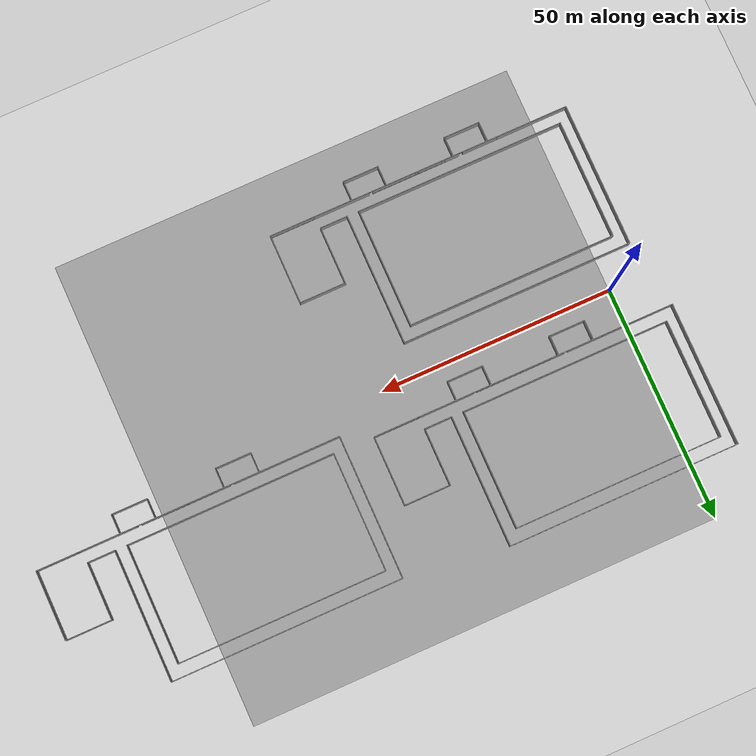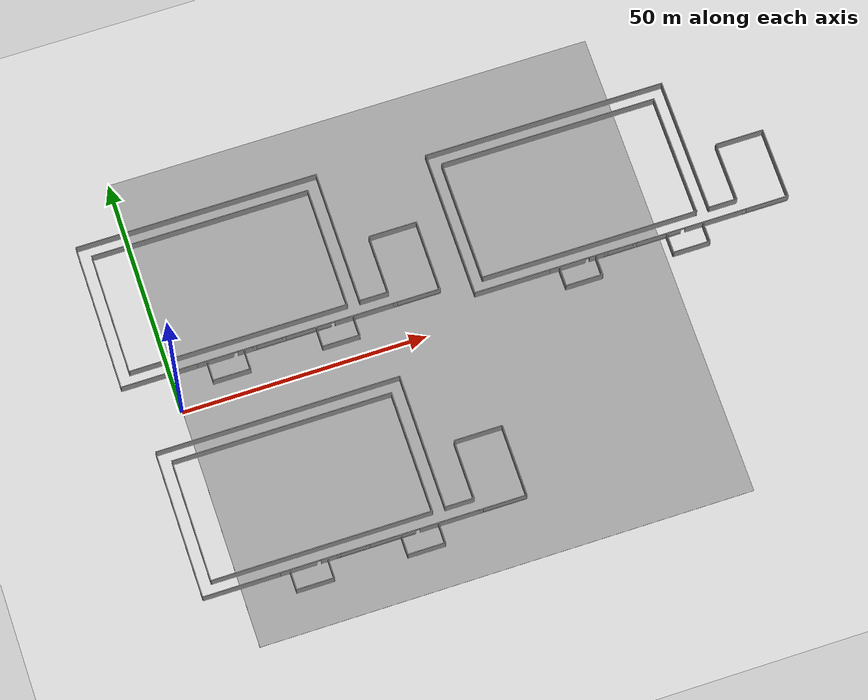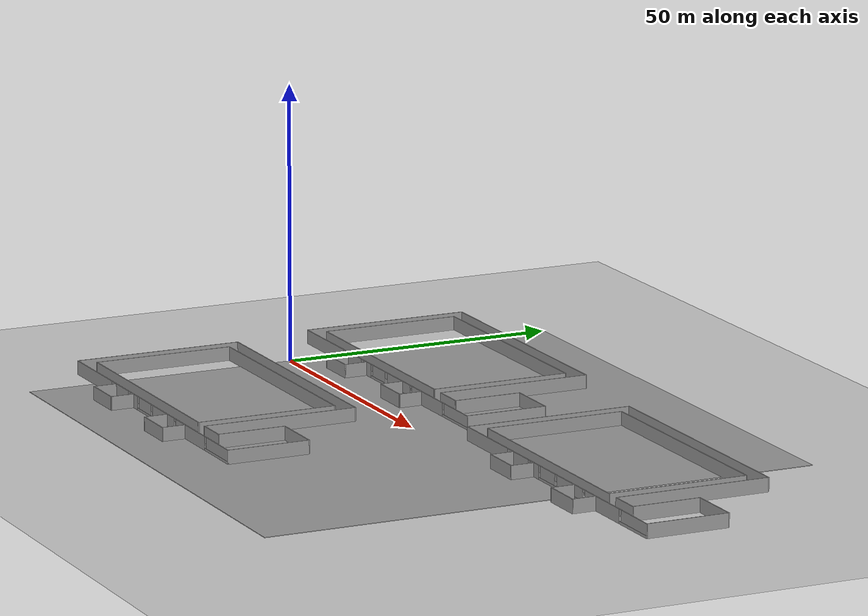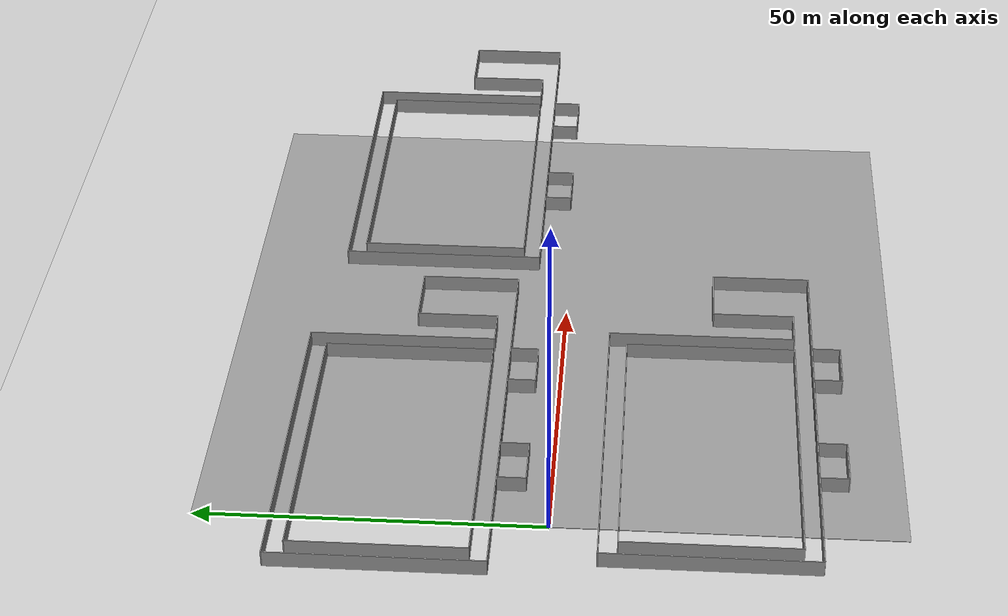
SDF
<sdf version="1.6">
 <world name="default">
  <light name="sun" type="directional">
   <pose>0 0 10 0 -0 0</pose>
   <diffuse>0.8 0.8 0.8 1</diffuse>
   <specular>0.2 0.2 0.2 1</specular>
   <attenuation>
    <range>1000</range>
    <constant>0.9</constant>
    <linear>0.01</linear>
    <quadratic>0.001</quadratic>
   </attenuation>
   <direction>-0.5 0.1 -0.9</direction>
  </light>
  <model name="ground_plane">
   <static>1</static>
   <link name="link">
    <collision name="collision">
     <geometry><plane><normal>0 0 1</normal><size>100 100</size></plane></geometry>
     <surface>
      <contact><collide_bitmask>65535</collide_bitmask></contact>
      <friction><ode><mu>100</mu><mu2>50</mu2></ode></friction>
     </surface>
    </collision>
    <visual name="visual">
     <cast_shadows>0</cast_shadows>
     <geometry><plane><normal>0 0 1</normal><size>100 100</size></plane></geometry>
     <material>
      <script><uri>file://media/materials/scripts/gazebo.material</uri><name>Gazebo/Grey</name></script>
     </material>
    </visual>
   </link>
  </model>
  <gravity>0 0 -9.8</gravity>
  <magnetic_field>6e-06 2.3e-05 -4.2e-05</magnetic_field>
  <atmosphere type="adiabatic"/>
  <physics name="default_physics" default="0" type="ode">
   <max_step_size>0.001</max_step_size>
   <real_time_factor>1</real_time_factor>
   <real_time_update_rate>1000</real_time_update_rate>
  </physics>
  <scene><ambient>0.4 0.4 0.4 1</ambient><background>0.7 0.7 0.7 1</background><shadows>1</shadows></scene>
  <spherical_coordinates>
   <surface_model>EARTH_WGS84</surface_model>
   <latitude_deg>0</latitude_deg>
   <longitude_deg>0</longitude_deg>
   <elevation>0</elevation>
   <heading_deg>0</heading_deg>
  </spherical_coordinates>
  <model name="ground_plane_0">
   <static>1</static>
   <link name="link">
    <collision name="collision">
     <geometry><plane><normal>0 0 1</normal><size>100 100</size></plane></geometry>
     <surface>
      <contact><collide_bitmask>65535</collide_bitmask></contact>
      <friction><ode><mu>100</mu><mu2>50</mu2></ode></friction>
     </surface>
    </collision>
    <visual name="visual">
     <cast_shadows>0</cast_shadows>
     <geometry><plane><normal>0 0 1</normal><size>100 100</size></plane></geometry>
     <material>
      <script><uri>file://media/materials/scripts/gazebo.material</uri><name>Gazebo/Grey</name></script>
     </material>
    </visual>
   </link>
   <pose>50.0335 0.140293 0 0 -0 0</pose>
  </model>
  <model name="my_worlds">
   <link name="myworld::myworld::Wall_0">
    <pose>7.725 -15.35 0 0 -0 0</pose>
    <visual name="Wall_0_Visual_6">
     <pose>-2.17588 0 1.5 0 -0 0</pose>
     <geometry><box><size>9.2769 0.15 2</size></box></geometry>
     <material>
      <script><uri>file://media/materials/scripts/gazebo.material</uri><name>Gazebo/Grey</name></script>
      <ambient>1 1 1 1</ambient>
      <shader type="pixel"/>
     </material>
     <meta><layer>0</layer></meta>
    </visual>
    <visual name="Wall_0_Visual_0">
     <pose>-21.2249 0 1.25 0 -0 0</pose>
     <geometry><box><size>7.55013 0.15 2.5</size></box></geometry>
     <material>
      <script><uri>file://media/materials/scripts/gazebo.material</uri><name>Gazebo/Grey</name></script>
      <ambient>1 1 1 1</ambient>
      <shader type="pixel"/>
     </material>
     <meta><layer>0</layer></meta>
    </visual>
    <visual name="Wall_0_Visual_14">
     <pose>2.86257 0 2.25 0 -0 0</pose>
     <geometry><box><size>0.8 0.15 0.5</size></box></geometry>
     <material>
      <script><uri>file://media/materials/scripts/gazebo.material</uri><name>Gazebo/Grey</name></script>
      <ambient>1 1 1 1</ambient>
      <shader type="pixel"/>
     </material>
     <meta><layer>0</layer></meta>
    </visual>
    <visual name="Wall_0_Visual_8">
     <pose>20.5547 0 1.5 0 -0 0</pose>
     <geometry><box><size>8.89059 0.15 2</size></box></geometry>
     <material>
      <script><uri>file://media/materials/scripts/gazebo.material</uri><name>Gazebo/Grey</name></script>
      <ambient>1 1 1 1</ambient>
      <shader type="pixel"/>
     </material>
     <meta><layer>0</layer></meta>
    </visual>
    <visual name="Wall_0_Visual_2">
     <pose>9.28599 0 1.25 0 -0 0</pose>
     <geometry><box><size>12.0468 0.15 2.5</size></box></geometry>
     <material>
      <script><uri>file://media/materials/scripts/gazebo.material</uri><name>Gazebo/Grey</name></script>
      <ambient>1 1 1 1</ambient>
      <shader type="pixel"/>
     </material>
     <meta><layer>0</layer></meta>
    </visual>
    <visual name="Wall_0_Visual_1">
     <pose>-15.1089 0 1.25 0 -0 0</pose>
     <geometry><box><size>3.08192 0.15 2.5</size></box></geometry>
     <material>
      <script><uri>file://media/materials/scripts/gazebo.material</uri><name>Gazebo/Grey</name></script>
      <ambient>1 1 1 1</ambient>
      <shader type="pixel"/>
     </material>
     <meta><layer>0</layer></meta>
    </visual>
    <visual name="Wall_0_Visual_3">
     <pose>-5.55269 0 0.25 0 -0 0</pose>
     <geometry><box><size>16.0305 0.15 0.5</size></box></geometry>
     <material>
      <script><uri>file://media/materials/scripts/gazebo.material</uri><name>Gazebo/Grey</name></script>
      <ambient>1 1 1 1</ambient>
      <shader type="pixel"/>
     </material>
     <meta><layer>0</layer></meta>
    </visual>
    <visual name="Wall_0_Visual_5">
     <pose>-10.1911 0 1.5 0 -0 0</pose>
     <geometry><box><size>5.15362 0.15 2</size></box></geometry>
     <material>
      <script><uri>file://media/materials/scripts/gazebo.material</uri><name>Gazebo/Grey</name></script>
      <ambient>1 1 1 1</ambient>
      <shader type="pixel"/>
     </material>
     <meta><layer>0</layer></meta>
    </visual>
    <visual name="Wall_0_Visual_13">
     <pose>2.86257 0 2.25 0 -0 0</pose>
     <geometry><box><size>0.8 0.15 0.5</size></box></geometry>
     <material>
      <script><uri>file://media/materials/scripts/gazebo.material</uri><name>Gazebo/Grey</name></script>
      <ambient>1 1 1 1</ambient>
      <shader type="pixel"/>
     </material>
     <meta><layer>0</layer></meta>
    </visual>
    <visual name="Wall_0_Visual_4">
     <pose>20.1547 0 0.25 0 -0 0</pose>
     <geometry><box><size>9.69059 0.15 0.5</size></box></geometry>
     <material>
      <script><uri>file://media/materials/scripts/gazebo.material</uri><name>Gazebo/Grey</name></script>
      <ambient>1 1 1 1</ambient>
      <shader type="pixel"/>
     </material>
     <meta><layer>0</layer></meta>
    </visual>
    <visual name="Wall_0_Visual_9">
     <pose>-13.1679 0 1.9 0 -0 0</pose>
     <geometry><box><size>0.8 0.15 1.2</size></box></geometry>
     <material>
      <script><uri>file://media/materials/scripts/gazebo.material</uri><name>Gazebo/Grey</name></script>
      <ambient>1 1 1 1</ambient>
      <shader type="pixel"/>
     </material>
     <meta><layer>0</layer></meta>
    </visual>
    <visual name="Wall_0_Visual_10">
     <pose>15.7094 0 1.9 0 -0 0</pose>
     <geometry><box><size>0.8 0.15 1.2</size></box></geometry>
     <material>
      <script><uri>file://media/materials/scripts/gazebo.material</uri><name>Gazebo/Grey</name></script>
      <ambient>1 1 1 1</ambient>
      <shader type="pixel"/>
     </material>
     <meta><layer>0</layer></meta>
    </visual>
    <visual name="Wall_0_Visual_11">
     <pose>-7.21433 0 1.9 0 -0 0</pose>
     <geometry><box><size>0.8 0.15 1.2</size></box></geometry>
     <material>
      <script><uri>file://media/materials/scripts/gazebo.material</uri><name>Gazebo/Grey</name></script>
      <ambient>1 1 1 1</ambient>
      <shader type="pixel"/>
     </material>
     <meta><layer>0</layer></meta>
    </visual>
    <visual name="Wall_0_Visual_12">
     <pose>-17.0499 0 2.25 0 -0 0</pose>
     <geometry><box><size>0.8 0.15 0.5</size></box></geometry>
     <material>
      <script><uri>file://media/materials/scripts/gazebo.material</uri><name>Gazebo/Grey</name></script>
      <ambient>1 1 1 1</ambient>
      <shader type="pixel"/>
     </material>
     <meta><layer>0</layer></meta>
    </visual>
    <visual name="Wall_0_Visual_7">
     <pose>-2.17588 0 1.5 0 -0 0</pose>
     <geometry><box><size>9.2769 0.15 2</size></box></geometry>
     <material>
      <script><uri>file://media/materials/scripts/gazebo.material</uri><name>Gazebo/Grey</name></script>
      <ambient>1 1 1 1</ambient>
      <shader type="pixel"/>
     </material>
     <meta><layer>0</layer></meta>
    </visual>
    <collision name="Wall_0_Collision_7">
     <pose>-2.17588 0 1.5 0 -0 0</pose>
     <geometry><box><size>9.2769 0.15 2</size></box></geometry>
     <surface>
      <friction>
       <ode><mu>1</mu><mu2>1</mu2><fdir1>0 0 0</fdir1><slip1>0</slip1><slip2>0</slip2></ode>
       <torsional>
        <coefficient>1</coefficient>
        <patch_radius>0</patch_radius>
        <surface_radius>0</surface_radius>
        <use_patch_radius>1</use_patch_radius>
        <ode><slip>0</slip></ode>
       </torsional>
      </friction>
      <bounce><restitution_coefficient>0</restitution_coefficient><threshold>1e+06</threshold></bounce>
      <contact>
       <collide_without_contact>0</collide_without_contact>
       <collide_without_contact_bitmask>1</collide_without_contact_bitmask>
       <collide_bitmask>1</collide_bitmask>
       <ode>
        <soft_cfm>0</soft_cfm>
        <soft_erp>0.2</soft_erp>
        <kp>1e+13</kp>
        <kd>1</kd>
        <max_vel>0.01</max_vel>
        <min_depth>0</min_depth>
       </ode>
       <bullet>
        <split_impulse>1</split_impulse>
        <split_impulse_penetration_threshold>-0.01</split_impulse_penetration_threshold>
        <soft_cfm>0</soft_cfm>
        <soft_erp>0.2</soft_erp>
        <kp>1e+13</kp>
        <kd>1</kd>
       </bullet>
      </contact>
     </surface>
    </collision>
    <collision name="Wall_0_Collision_13">
     <pose>2.86257 0 2.25 0 -0 0</pose>
     <geometry><box><size>0.8 0.15 0.5</size></box></geometry>
     <surface>
      <friction>
       <ode><mu>1</mu><mu2>1</mu2><fdir1>0 0 0</fdir1><slip1>0</slip1><slip2>0</slip2></ode>
       <torsional>
        <coefficient>1</coefficient>
        <patch_radius>0</patch_radius>
        <surface_radius>0</surface_radius>
        <use_patch_radius>1</use_patch_radius>
        <ode><slip>0</slip></ode>
       </torsional>
      </friction>
      <bounce><restitution_coefficient>0</restitution_coefficient><threshold>1e+06</threshold></bounce>
      <contact>
       <collide_without_contact>0</collide_without_contact>
       <collide_without_contact_bitmask>1</collide_without_contact_bitmask>
       <collide_bitmask>1</collide_bitmask>
       <ode>
        <soft_cfm>0</soft_cfm>
        <soft_erp>0.2</soft_erp>
        <kp>1e+13</kp>
        <kd>1</kd>
        <max_vel>0.01</max_vel>
        <min_depth>0</min_depth>
       </ode>
       <bullet>
        <split_impulse>1</split_impulse>
        <split_impulse_penetration_threshold>-0.01</split_impulse_penetration_threshold>
        <soft_cfm>0</soft_cfm>
        <soft_erp>0.2</soft_erp>
        <kp>1e+13</kp>
        <kd>1</kd>
       </bullet>
      </contact>
     </surface>
    </collision>
    <collision name="Wall_0_Collision_1">
     <pose>-15.1089 0 1.25 0 -0 0</pose>
     <geometry><box><size>3.08192 0.15 2.5</size></box></geometry>
     <surface>
      <friction>
       <ode><mu>1</mu><mu2>1</mu2><fdir1>0 0 0</fdir1><slip1>0</slip1><slip2>0</slip2></ode>
       <torsional>
        <coefficient>1</coefficient>
        <patch_radius>0</patch_radius>
        <surface_radius>0</surface_radius>
        <use_patch_radius>1</use_patch_radius>
        <ode><slip>0</slip></ode>
       </torsional>
      </friction>
      <bounce><restitution_coefficient>0</restitution_coefficient><threshold>1e+06</threshold></bounce>
      <contact>
       <collide_without_contact>0</collide_without_contact>
       <collide_without_contact_bitmask>1</collide_without_contact_bitmask>
       <collide_bitmask>1</collide_bitmask>
       <ode>
        <soft_cfm>0</soft_cfm>
        <soft_erp>0.2</soft_erp>
        <kp>1e+13</kp>
        <kd>1</kd>
        <max_vel>0.01</max_vel>
        <min_depth>0</min_depth>
       </ode>
       <bullet>
        <split_impulse>1</split_impulse>
        <split_impulse_penetration_threshold>-0.01</split_impulse_penetration_threshold>
        <soft_cfm>0</soft_cfm>
        <soft_erp>0.2</soft_erp>
        <kp>1e+13</kp>
        <kd>1</kd>
       </bullet>
      </contact>
     </surface>
    </collision>
    <collision name="Wall_0_Collision_11">
     <pose>-7.21433 0 1.9 0 -0 0</pose>
     <geometry><box><size>0.8 0.15 1.2</size></box></geometry>
     <surface>
      <friction>
       <ode><mu>1</mu><mu2>1</mu2><fdir1>0 0 0</fdir1><slip1>0</slip1><slip2>0</slip2></ode>
       <torsional>
        <coefficient>1</coefficient>
        <patch_radius>0</patch_radius>
        <surface_radius>0</surface_radius>
        <use_patch_radius>1</use_patch_radius>
        <ode><slip>0</slip></ode>
       </torsional>
      </friction>
      <bounce><restitution_coefficient>0</restitution_coefficient><threshold>1e+06</threshold></bounce>
      <contact>
       <collide_without_contact>0</collide_without_contact>
       <collide_without_contact_bitmask>1</collide_without_contact_bitmask>
       <collide_bitmask>1</collide_bitmask>
       <ode>
        <soft_cfm>0</soft_cfm>
        <soft_erp>0.2</soft_erp>
        <kp>1e+13</kp>
        <kd>1</kd>
        <max_vel>0.01</max_vel>
        <min_depth>0</min_depth>
       </ode>
       <bullet>
        <split_impulse>1</split_impulse>
        <split_impulse_penetration_threshold>-0.01</split_impulse_penetration_threshold>
        <soft_cfm>0</soft_cfm>
        <soft_erp>0.2</soft_erp>
        <kp>1e+13</kp>
        <kd>1</kd>
       </bullet>
      </contact>
     </surface>
    </collision>
    <collision name="Wall_0_Collision_14">
     <pose>2.86257 0 2.25 0 -0 0</pose>
     <geometry><box><size>0.8 0.15 0.5</size></box></geometry>
     <surface>
      <friction>
       <ode><mu>1</mu><mu2>1</mu2><fdir1>0 0 0</fdir1><slip1>0</slip1><slip2>0</slip2></ode>
       <torsional>
        <coefficient>1</coefficient>
        <patch_radius>0</patch_radius>
        <surface_radius>0</surface_radius>
        <use_patch_radius>1</use_patch_radius>
        <ode><slip>0</slip></ode>
       </torsional>
      </friction>
      <bounce><restitution_coefficient>0</restitution_coefficient><threshold>1e+06</threshold></bounce>
      <contact>
       <collide_without_contact>0</collide_without_contact>
       <collide_without_contact_bitmask>1</collide_without_contact_bitmask>
       <collide_bitmask>1</collide_bitmask>
       <ode>
        <soft_cfm>0</soft_cfm>
        <soft_erp>0.2</soft_erp>
        <kp>1e+13</kp>
        <kd>1</kd>
        <max_vel>0.01</max_vel>
        <min_depth>0</min_depth>
       </ode>
       <bullet>
        <split_impulse>1</split_impulse>
        <split_impulse_penetration_threshold>-0.01</split_impulse_penetration_threshold>
        <soft_cfm>0</soft_cfm>
        <soft_erp>0.2</soft_erp>
        <kp>1e+13</kp>
        <kd>1</kd>
       </bullet>
      </contact>
     </surface>
    </collision>
    <collision name="Wall_0_Collision_3">
     <pose>-5.55269 0 0.25 0 -0 0</pose>
     <geometry><box><size>16.0305 0.15 0.5</size></box></geometry>
     <surface>
      <friction>
       <ode><mu>1</mu><mu2>1</mu2><fdir1>0 0 0</fdir1><slip1>0</slip1><slip2>0</slip2></ode>
       <torsional>
        <coefficient>1</coefficient>
        <patch_radius>0</patch_radius>
        <surface_radius>0</surface_radius>
        <use_patch_radius>1</use_patch_radius>
        <ode><slip>0</slip></ode>
       </torsional>
      </friction>
      <bounce><restitution_coefficient>0</restitution_coefficient><threshold>1e+06</threshold></bounce>
      <contact>
       <collide_without_contact>0</collide_without_contact>
       <collide_without_contact_bitmask>1</collide_without_contact_bitmask>
       <collide_bitmask>1</collide_bitmask>
       <ode>
        <soft_cfm>0</soft_cfm>
        <soft_erp>0.2</soft_erp>
        <kp>1e+13</kp>
        <kd>1</kd>
        <max_vel>0.01</max_vel>
        <min_depth>0</min_depth>
       </ode>
       <bullet>
        <split_impulse>1</split_impulse>
        <split_impulse_penetration_threshold>-0.01</split_impulse_penetration_threshold>
        <soft_cfm>0</soft_cfm>
        <soft_erp>0.2</soft_erp>
        <kp>1e+13</kp>
        <kd>1</kd>
       </bullet>
      </contact>
     </surface>
    </collision>
    <collision name="Wall_0_Collision_5">
     <pose>-10.1911 0 1.5 0 -0 0</pose>
     <geometry><box><size>5.15362 0.15 2</size></box></geometry>
     <surface>
      <friction>
       <ode><mu>1</mu><mu2>1</mu2><fdir1>0 0 0</fdir1><slip1>0</slip1><slip2>0</slip2></ode>
       <torsional>
        <coefficient>1</coefficient>
        <patch_radius>0</patch_radius>
        <surface_radius>0</surface_radius>
        <use_patch_radius>1</use_patch_radius>
        <ode><slip>0</slip></ode>
       </torsional>
      </friction>
      <bounce><restitution_coefficient>0</restitution_coefficient><threshold>1e+06</threshold></bounce>
      <contact>
       <collide_without_contact>0</collide_without_contact>
       <collide_without_contact_bitmask>1</collide_without_contact_bitmask>
       <collide_bitmask>1</collide_bitmask>
       <ode>
        <soft_cfm>0</soft_cfm>
        <soft_erp>0.2</soft_erp>
        <kp>1e+13</kp>
        <kd>1</kd>
        <max_vel>0.01</max_vel>
        <min_depth>0</min_depth>
       </ode>
       <bullet>
        <split_impulse>1</split_impulse>
        <split_impulse_penetration_threshold>-0.01</split_impulse_penetration_threshold>
        <soft_cfm>0</soft_cfm>
        <soft_erp>0.2</soft_erp>
        <kp>1e+13</kp>
        <kd>1</kd>
       </bullet>
      </contact>
     </surface>
    </collision>
    <collision name="Wall_0_Collision_2">
     <pose>9.28599 0 1.25 0 -0 0</pose>
     <geometry><box><size>12.0468 0.15 2.5</size></box></geometry>
     <surface>
      <friction>
       <ode><mu>1</mu><mu2>1</mu2><fdir1>0 0 0</fdir1><slip1>0</slip1><slip2>0</slip2></ode>
       <torsional>
        <coefficient>1</coefficient>
        <patch_radius>0</patch_radius>
        <surface_radius>0</surface_radius>
        <use_patch_radius>1</use_patch_radius>
        <ode><slip>0</slip></ode>
       </torsional>
      </friction>
      <bounce><restitution_coefficient>0</restitution_coefficient><threshold>1e+06</threshold></bounce>
      <contact>
       <collide_without_contact>0</collide_without_contact>
       <collide_without_contact_bitmask>1</collide_without_contact_bitmask>
       <collide_bitmask>1</collide_bitmask>
       <ode>
        <soft_cfm>0</soft_cfm>
        <soft_erp>0.2</soft_erp>
        <kp>1e+13</kp>
        <kd>1</kd>
        <max_vel>0.01</max_vel>
        <min_depth>0</min_depth>
       </ode>
       <bullet>
        <split_impulse>1</split_impulse>
        <split_impulse_penetration_threshold>-0.01</split_impulse_penetration_threshold>
        <soft_cfm>0</soft_cfm>
        <soft_erp>0.2</soft_erp>
        <kp>1e+13</kp>
        <kd>1</kd>
       </bullet>
      </contact>
     </surface>
    </collision>
    <collision name="Wall_0_Collision_6">
     <pose>-2.17588 0 1.5 0 -0 0</pose>
     <geometry><box><size>9.2769 0.15 2</size></box></geometry>
     <surface>
      <friction>
       <ode><mu>1</mu><mu2>1</mu2><fdir1>0 0 0</fdir1><slip1>0</slip1><slip2>0</slip2></ode>
       <torsional>
        <coefficient>1</coefficient>
        <patch_radius>0</patch_radius>
        <surface_radius>0</surface_radius>
        <use_patch_radius>1</use_patch_radius>
        <ode><slip>0</slip></ode>
       </torsional>
      </friction>
      <bounce><restitution_coefficient>0</restitution_coefficient><threshold>1e+06</threshold></bounce>
      <contact>
       <collide_without_contact>0</collide_without_contact>
       <collide_without_contact_bitmask>1</collide_without_contact_bitmask>
       <collide_bitmask>1</collide_bitmask>
       <ode>
        <soft_cfm>0</soft_cfm>
        <soft_erp>0.2</soft_erp>
        <kp>1e+13</kp>
        <kd>1</kd>
        <max_vel>0.01</max_vel>
        <min_depth>0</min_depth>
       </ode>
       <bullet>
        <split_impulse>1</split_impulse>
        <split_impulse_penetration_threshold>-0.01</split_impulse_penetration_threshold>
        <soft_cfm>0</soft_cfm>
        <soft_erp>0.2</soft_erp>
        <kp>1e+13</kp>
        <kd>1</kd>
       </bullet>
      </contact>
     </surface>
    </collision>
    <collision name="Wall_0_Collision_12">
     <pose>-17.0499 0 2.25 0 -0 0</pose>
     <geometry><box><size>0.8 0.15 0.5</size></box></geometry>
     <surface>
      <friction>
       <ode><mu>1</mu><mu2>1</mu2><fdir1>0 0 0</fdir1><slip1>0</slip1><slip2>0</slip2></ode>
       <torsional>
        <coefficient>1</coefficient>
        <patch_radius>0</patch_radius>
        <surface_radius>0</surface_radius>
        <use_patch_radius>1</use_patch_radius>
        <ode><slip>0</slip></ode>
       </torsional>
      </friction>
      <bounce><restitution_coefficient>0</restitution_coefficient><threshold>1e+06</threshold></bounce>
      <contact>
       <collide_without_contact>0</collide_without_contact>
       <collide_without_contact_bitmask>1</collide_without_contact_bitmask>
       <collide_bitmask>1</collide_bitmask>
       <ode>
        <soft_cfm>0</soft_cfm>
        <soft_erp>0.2</soft_erp>
        <kp>1e+13</kp>
        <kd>1</kd>
        <max_vel>0.01</max_vel>
        <min_depth>0</min_depth>
       </ode>
       <bullet>
        <split_impulse>1</split_impulse>
        <split_impulse_penetration_threshold>-0.01</split_impulse_penetration_threshold>
        <soft_cfm>0</soft_cfm>
        <soft_erp>0.2</soft_erp>
        <kp>1e+13</kp>
        <kd>1</kd>
       </bullet>
      </contact>
     </surface>
    </collision>
    <collision name="Wall_0_Collision_0">
     <pose>-21.2249 0 1.25 0 -0 0</pose>
     <geometry><box><size>7.55013 0.15 2.5</size></box></geometry>
     <surface>
      <friction>
       <ode><mu>1</mu><mu2>1</mu2><fdir1>0 0 0</fdir1><slip1>0</slip1><slip2>0</slip2></ode>
       <torsional>
        <coefficient>1</coefficient>
        <patch_radius>0</patch_radius>
        <surface_radius>0</surface_radius>
        <use_patch_radius>1</use_patch_radius>
        <ode><slip>0</slip></ode>
       </torsional>
      </friction>
      <bounce><restitution_coefficient>0</restitution_coefficient><threshold>1e+06</threshold></bounce>
      <contact>
       <collide_without_contact>0</collide_without_contact>
       <collide_without_contact_bitmask>1</collide_without_contact_bitmask>
       <collide_bitmask>1</collide_bitmask>
       <ode>
        <soft_cfm>0</soft_cfm>
        <soft_erp>0.2</soft_erp>
        <kp>1e+13</kp>
        <kd>1</kd>
        <max_vel>0.01</max_vel>
        <min_depth>0</min_depth>
       </ode>
       <bullet>
        <split_impulse>1</split_impulse>
        <split_impulse_penetration_threshold>-0.01</split_impulse_penetration_threshold>
        <soft_cfm>0</soft_cfm>
        <soft_erp>0.2</soft_erp>
        <kp>1e+13</kp>
        <kd>1</kd>
       </bullet>
      </contact>
     </surface>
    </collision>
    <collision name="Wall_0_Collision_8">
     <pose>20.5547 0 1.5 0 -0 0</pose>
     <geometry><box><size>8.89059 0.15 2</size></box></geometry>
     <surface>
      <friction>
       <ode><mu>1</mu><mu2>1</mu2><fdir1>0 0 0</fdir1><slip1>0</slip1><slip2>0</slip2></ode>
       <torsional>
        <coefficient>1</coefficient>
        <patch_radius>0</patch_radius>
        <surface_radius>0</surface_radius>
        <use_patch_radius>1</use_patch_radius>
        <ode><slip>0</slip></ode>
       </torsional>
      </friction>
      <bounce><restitution_coefficient>0</restitution_coefficient><threshold>1e+06</threshold></bounce>
      <contact>
       <collide_without_contact>0</collide_without_contact>
       <collide_without_contact_bitmask>1</collide_without_contact_bitmask>
       <collide_bitmask>1</collide_bitmask>
       <ode>
        <soft_cfm>0</soft_cfm>
        <soft_erp>0.2</soft_erp>
        <kp>1e+13</kp>
        <kd>1</kd>
        <max_vel>0.01</max_vel>
        <min_depth>0</min_depth>
       </ode>
       <bullet>
        <split_impulse>1</split_impulse>
        <split_impulse_penetration_threshold>-0.01</split_impulse_penetration_threshold>
        <soft_cfm>0</soft_cfm>
        <soft_erp>0.2</soft_erp>
        <kp>1e+13</kp>
        <kd>1</kd>
       </bullet>
      </contact>
     </surface>
    </collision>
    <collision name="Wall_0_Collision_4">
     <pose>20.1547 0 0.25 0 -0 0</pose>
     <geometry><box><size>9.69059 0.15 0.5</size></box></geometry>
     <surface>
      <friction>
       <ode><mu>1</mu><mu2>1</mu2><fdir1>0 0 0</fdir1><slip1>0</slip1><slip2>0</slip2></ode>
       <torsional>
        <coefficient>1</coefficient>
        <patch_radius>0</patch_radius>
        <surface_radius>0</surface_radius>
        <use_patch_radius>1</use_patch_radius>
        <ode><slip>0</slip></ode>
       </torsional>
      </friction>
      <bounce><restitution_coefficient>0</restitution_coefficient><threshold>1e+06</threshold></bounce>
      <contact>
       <collide_without_contact>0</collide_without_contact>
       <collide_without_contact_bitmask>1</collide_without_contact_bitmask>
       <collide_bitmask>1</collide_bitmask>
       <ode>
        <soft_cfm>0</soft_cfm>
        <soft_erp>0.2</soft_erp>
        <kp>1e+13</kp>
        <kd>1</kd>
        <max_vel>0.01</max_vel>
        <min_depth>0</min_depth>
       </ode>
       <bullet>
        <split_impulse>1</split_impulse>
        <split_impulse_penetration_threshold>-0.01</split_impulse_penetration_threshold>
        <soft_cfm>0</soft_cfm>
        <soft_erp>0.2</soft_erp>
        <kp>1e+13</kp>
        <kd>1</kd>
       </bullet>
      </contact>
     </surface>
    </collision>
    <collision name="Wall_0_Collision_10">
     <pose>15.7094 0 1.9 0 -0 0</pose>
     <geometry><box><size>0.8 0.15 1.2</size></box></geometry>
     <surface>
      <friction>
       <ode><mu>1</mu><mu2>1</mu2><fdir1>0 0 0</fdir1><slip1>0</slip1><slip2>0</slip2></ode>
       <torsional>
        <coefficient>1</coefficient>
        <patch_radius>0</patch_radius>
        <surface_radius>0</surface_radius>
        <use_patch_radius>1</use_patch_radius>
        <ode><slip>0</slip></ode>
       </torsional>
      </friction>
      <bounce><restitution_coefficient>0</restitution_coefficient><threshold>1e+06</threshold></bounce>
      <contact>
       <collide_without_contact>0</collide_without_contact>
       <collide_without_contact_bitmask>1</collide_without_contact_bitmask>
       <collide_bitmask>1</collide_bitmask>
       <ode>
        <soft_cfm>0</soft_cfm>
        <soft_erp>0.2</soft_erp>
        <kp>1e+13</kp>
        <kd>1</kd>
        <max_vel>0.01</max_vel>
        <min_depth>0</min_depth>
       </ode>
       <bullet>
        <split_impulse>1</split_impulse>
        <split_impulse_penetration_threshold>-0.01</split_impulse_penetration_threshold>
        <soft_cfm>0</soft_cfm>
        <soft_erp>0.2</soft_erp>
        <kp>1e+13</kp>
        <kd>1</kd>
       </bullet>
      </contact>
     </surface>
    </collision>
    <collision name="Wall_0_Collision_9">
     <pose>-13.1679 0 1.9 0 -0 0</pose>
     <geometry><box><size>0.8 0.15 1.2</size></box></geometry>
     <surface>
      <friction>
       <ode><mu>1</mu><mu2>1</mu2><fdir1>0 0 0</fdir1><slip1>0</slip1><slip2>0</slip2></ode>
       <torsional>
        <coefficient>1</coefficient>
        <patch_radius>0</patch_radius>
        <surface_radius>0</surface_radius>
        <use_patch_radius>1</use_patch_radius>
        <ode><slip>0</slip></ode>
       </torsional>
      </friction>
      <bounce><restitution_coefficient>0</restitution_coefficient><threshold>1e+06</threshold></bounce>
      <contact>
       <collide_without_contact>0</collide_without_contact>
       <collide_without_contact_bitmask>1</collide_without_contact_bitmask>
       <collide_bitmask>1</collide_bitmask>
       <ode>
        <soft_cfm>0</soft_cfm>
        <soft_erp>0.2</soft_erp>
        <kp>1e+13</kp>
        <kd>1</kd>
        <max_vel>0.01</max_vel>
        <min_depth>0</min_depth>
       </ode>
       <bullet>
        <split_impulse>1</split_impulse>
        <split_impulse_penetration_threshold>-0.01</split_impulse_penetration_threshold>
        <soft_cfm>0</soft_cfm>
        <soft_erp>0.2</soft_erp>
        <kp>1e+13</kp>
        <kd>1</kd>
       </bullet>
      </contact>
     </surface>
    </collision>
   </link>
   <link name="myworld::myworld::Wall_11">
    <pose>19.875 -12.75 0 0 -0 3.14159</pose>
    <visual name="Wall_11_Visual">
     <pose>0 0 1.25 0 -0 0</pose>
     <geometry><box><size>6 0.15 2.5</size></box></geometry>
     <material>
      <script><uri>file://media/materials/scripts/gazebo.material</uri><name>Gazebo/Grey</name></script>
      <ambient>1 1 1 1</ambient>
      <shader type="pixel"/>
     </material>
     <meta><layer>0</layer></meta>
    </visual>
    <collision name="Wall_11_Collision">
     <pose>0 0 1.25 0 -0 0</pose>
     <geometry><box><size>6 0.15 2.5</size></box></geometry>
     <surface>
      <friction>
       <ode><mu>1</mu><mu2>1</mu2><fdir1>0 0 0</fdir1><slip1>0</slip1><slip2>0</slip2></ode>
       <torsional>
        <coefficient>1</coefficient>
        <patch_radius>0</patch_radius>
        <surface_radius>0</surface_radius>
        <use_patch_radius>1</use_patch_radius>
        <ode><slip>0</slip></ode>
       </torsional>
      </friction>
      <bounce><restitution_coefficient>0</restitution_coefficient><threshold>1e+06</threshold></bounce>
      <contact>
       <collide_without_contact>0</collide_without_contact>
       <collide_without_contact_bitmask>1</collide_without_contact_bitmask>
       <collide_bitmask>1</collide_bitmask>
       <ode>
        <soft_cfm>0</soft_cfm>
        <soft_erp>0.2</soft_erp>
        <kp>1e+13</kp>
        <kd>1</kd>
        <max_vel>0.01</max_vel>
        <min_depth>0</min_depth>
       </ode>
       <bullet>
        <split_impulse>1</split_impulse>
        <split_impulse_penetration_threshold>-0.01</split_impulse_penetration_threshold>
        <soft_cfm>0</soft_cfm>
        <soft_erp>0.2</soft_erp>
        <kp>1e+13</kp>
        <kd>1</kd>
       </bullet>
      </contact>
     </surface>
    </collision>
   </link>
   <link name="myworld::myworld::Wall_12">
    <pose>16.95 1.3 0 0 -0 1.5708</pose>
    <visual name="Wall_12_Visual">
     <pose>0 0 1.25 0 -0 0</pose>
     <geometry><box><size>28.25 0.15 2.5</size></box></geometry>
     <material>
      <script><uri>file://media/materials/scripts/gazebo.material</uri><name>Gazebo/Grey</name></script>
      <ambient>1 1 1 1</ambient>
      <shader type="pixel"/>
     </material>
     <meta><layer>0</layer></meta>
    </visual>
    <collision name="Wall_12_Collision">
     <pose>0 0 1.25 0 -0 0</pose>
     <geometry><box><size>28.25 0.15 2.5</size></box></geometry>
     <surface>
      <friction>
       <ode><mu>1</mu><mu2>1</mu2><fdir1>0 0 0</fdir1><slip1>0</slip1><slip2>0</slip2></ode>
       <torsional>
        <coefficient>1</coefficient>
        <patch_radius>0</patch_radius>
        <surface_radius>0</surface_radius>
        <use_patch_radius>1</use_patch_radius>
        <ode><slip>0</slip></ode>
       </torsional>
      </friction>
      <bounce><restitution_coefficient>0</restitution_coefficient><threshold>1e+06</threshold></bounce>
      <contact>
       <collide_without_contact>0</collide_without_contact>
       <collide_without_contact_bitmask>1</collide_without_contact_bitmask>
       <collide_bitmask>1</collide_bitmask>
       <ode>
        <soft_cfm>0</soft_cfm>
        <soft_erp>0.2</soft_erp>
        <kp>1e+13</kp>
        <kd>1</kd>
        <max_vel>0.01</max_vel>
        <min_depth>0</min_depth>
       </ode>
       <bullet>
        <split_impulse>1</split_impulse>
        <split_impulse_penetration_threshold>-0.01</split_impulse_penetration_threshold>
        <soft_cfm>0</soft_cfm>
        <soft_erp>0.2</soft_erp>
        <kp>1e+13</kp>
        <kd>1</kd>
       </bullet>
      </contact>
     </surface>
    </collision>
   </link>
   <link name="myworld::myworld::Wall_13">
    <pose>-7.85 15.35 0 0 -0 3.14159</pose>
    <visual name="Wall_13_Visual">
     <pose>0 0 1.25 0 -0 0</pose>
     <geometry><box><size>49.75 0.15 2.5</size></box></geometry>
     <material>
      <script><uri>file://media/materials/scripts/gazebo.material</uri><name>Gazebo/Grey</name></script>
      <ambient>1 1 1 1</ambient>
      <shader type="pixel"/>
     </material>
     <meta><layer>0</layer></meta>
    </visual>
    <collision name="Wall_13_Collision">
     <pose>0 0 1.25 0 -0 0</pose>
     <geometry><box><size>49.75 0.15 2.5</size></box></geometry>
     <surface>
      <friction>
       <ode><mu>1</mu><mu2>1</mu2><fdir1>0 0 0</fdir1><slip1>0</slip1><slip2>0</slip2></ode>
       <torsional>
        <coefficient>1</coefficient>
        <patch_radius>0</patch_radius>
        <surface_radius>0</surface_radius>
        <use_patch_radius>1</use_patch_radius>
        <ode><slip>0</slip></ode>
       </torsional>
      </friction>
      <bounce><restitution_coefficient>0</restitution_coefficient><threshold>1e+06</threshold></bounce>
      <contact>
       <collide_without_contact>0</collide_without_contact>
       <collide_without_contact_bitmask>1</collide_without_contact_bitmask>
       <collide_bitmask>1</collide_bitmask>
       <ode>
        <soft_cfm>0</soft_cfm>
        <soft_erp>0.2</soft_erp>
        <kp>1e+13</kp>
        <kd>1</kd>
        <max_vel>0.01</max_vel>
        <min_depth>0</min_depth>
       </ode>
       <bullet>
        <split_impulse>1</split_impulse>
        <split_impulse_penetration_threshold>-0.01</split_impulse_penetration_threshold>
        <soft_cfm>0</soft_cfm>
        <soft_erp>0.2</soft_erp>
        <kp>1e+13</kp>
        <kd>1</kd>
       </bullet>
      </contact>
     </surface>
    </collision>
   </link>
   <link name="myworld::myworld::Wall_14">
    <pose>-32.65 0.024999 0 0 0 -1.5708</pose>
    <visual name="Wall_14_Visual">
     <pose>0 0 1.25 0 -0 0</pose>
     <geometry><box><size>30.8 0.15 2.5</size></box></geometry>
     <material>
      <script><uri>file://media/materials/scripts/gazebo.material</uri><name>Gazebo/Grey</name></script>
      <ambient>1 1 1 1</ambient>
      <shader type="pixel"/>
     </material>
     <meta><layer>0</layer></meta>
    </visual>
    <collision name="Wall_14_Collision">
     <pose>0 0 1.25 0 -0 0</pose>
     <geometry><box><size>30.8 0.15 2.5</size></box></geometry>
     <surface>
      <friction>
       <ode><mu>1</mu><mu2>1</mu2><fdir1>0 0 0</fdir1><slip1>0</slip1><slip2>0</slip2></ode>
       <torsional>
        <coefficient>1</coefficient>
        <patch_radius>0</patch_radius>
        <surface_radius>0</surface_radius>
        <use_patch_radius>1</use_patch_radius>
        <ode><slip>0</slip></ode>
       </torsional>
      </friction>
      <bounce><restitution_coefficient>0</restitution_coefficient><threshold>1e+06</threshold></bounce>
      <contact>
       <collide_without_contact>0</collide_without_contact>
       <collide_without_contact_bitmask>1</collide_without_contact_bitmask>
       <collide_bitmask>1</collide_bitmask>
       <ode>
        <soft_cfm>0</soft_cfm>
        <soft_erp>0.2</soft_erp>
        <kp>1e+13</kp>
        <kd>1</kd>
        <max_vel>0.01</max_vel>
        <min_depth>0</min_depth>
       </ode>
       <bullet>
        <split_impulse>1</split_impulse>
        <split_impulse_penetration_threshold>-0.01</split_impulse_penetration_threshold>
        <soft_cfm>0</soft_cfm>
        <soft_erp>0.2</soft_erp>
        <kp>1e+13</kp>
        <kd>1</kd>
       </bullet>
      </contact>
     </surface>
    </collision>
   </link>
   <link name="myworld::myworld::Wall_16">
    <pose>-24.875 -15.35 0 0 -0 3.14159</pose>
    <visual name="Wall_16_Visual">
     <pose>0 0 1.25 0 -0 0</pose>
     <geometry><box><size>15.5 0.15 2.5</size></box></geometry>
     <material>
      <script><uri>file://media/materials/scripts/gazebo.material</uri><name>Gazebo/Grey</name></script>
      <ambient>1 1 1 1</ambient>
      <shader type="pixel"/>
     </material>
     <meta><layer>0</layer></meta>
    </visual>
    <collision name="Wall_16_Collision">
     <pose>0 0 1.25 0 -0 0</pose>
     <geometry><box><size>15.5 0.15 2.5</size></box></geometry>
     <surface>
      <friction>
       <ode><mu>1</mu><mu2>1</mu2><fdir1>0 0 0</fdir1><slip1>0</slip1><slip2>0</slip2></ode>
       <torsional>
        <coefficient>1</coefficient>
        <patch_radius>0</patch_radius>
        <surface_radius>0</surface_radius>
        <use_patch_radius>1</use_patch_radius>
        <ode><slip>0</slip></ode>
       </torsional>
      </friction>
      <bounce><restitution_coefficient>0</restitution_coefficient><threshold>1e+06</threshold></bounce>
      <contact>
       <collide_without_contact>0</collide_without_contact>
       <collide_without_contact_bitmask>1</collide_without_contact_bitmask>
       <collide_bitmask>1</collide_bitmask>
       <ode>
        <soft_cfm>0</soft_cfm>
        <soft_erp>0.2</soft_erp>
        <kp>1e+13</kp>
        <kd>1</kd>
        <max_vel>0.01</max_vel>
        <min_depth>0</min_depth>
       </ode>
       <bullet>
        <split_impulse>1</split_impulse>
        <split_impulse_penetration_threshold>-0.01</split_impulse_penetration_threshold>
        <soft_cfm>0</soft_cfm>
        <soft_erp>0.2</soft_erp>
        <kp>1e+13</kp>
        <kd>1</kd>
       </bullet>
      </contact>
     </surface>
    </collision>
   </link>
   <link name="myworld::myworld::Wall_2">
    <pose>32.65 -7.925 0 0 -0 1.5708</pose>
    <visual name="Wall_2_Visual">
     <pose>0 0 1.25 0 -0 0</pose>
     <geometry><box><size>15 0.15 2.5</size></box></geometry>
     <material>
      <script><uri>file://media/materials/scripts/gazebo.material</uri><name>Gazebo/Grey</name></script>
      <ambient>1 1 1 1</ambient>
      <shader type="pixel"/>
     </material>
     <meta><layer>0</layer></meta>
    </visual>
    <collision name="Wall_2_Collision">
     <pose>0 0 1.25 0 -0 0</pose>
     <geometry><box><size>15 0.15 2.5</size></box></geometry>
     <surface>
      <friction>
       <ode><mu>1</mu><mu2>1</mu2><fdir1>0 0 0</fdir1><slip1>0</slip1><slip2>0</slip2></ode>
       <torsional>
        <coefficient>1</coefficient>
        <patch_radius>0</patch_radius>
        <surface_radius>0</surface_radius>
        <use_patch_radius>1</use_patch_radius>
        <ode><slip>0</slip></ode>
       </torsional>
      </friction>
      <bounce><restitution_coefficient>0</restitution_coefficient><threshold>1e+06</threshold></bounce>
      <contact>
       <collide_without_contact>0</collide_without_contact>
       <collide_without_contact_bitmask>1</collide_without_contact_bitmask>
       <collide_bitmask>1</collide_bitmask>
       <ode>
        <soft_cfm>0</soft_cfm>
        <soft_erp>0.2</soft_erp>
        <kp>1e+13</kp>
        <kd>1</kd>
        <max_vel>0.01</max_vel>
        <min_depth>0</min_depth>
       </ode>
       <bullet>
        <split_impulse>1</split_impulse>
        <split_impulse_penetration_threshold>-0.01</split_impulse_penetration_threshold>
        <soft_cfm>0</soft_cfm>
        <soft_erp>0.2</soft_erp>
        <kp>1e+13</kp>
        <kd>1</kd>
       </bullet>
      </contact>
     </surface>
    </collision>
   </link>
   <link name="myworld::myworld::Wall_20">
    <pose>14.3513 -0.043041 0 0 -0 1.5708</pose>
    <visual name="Wall_20_Visual">
     <pose>0 0 1.25 0 -0 0</pose>
     <geometry><box><size>25.5 0.15 2.5</size></box></geometry>
     <material>
      <script><uri>file://media/materials/scripts/gazebo.material</uri><name>Gazebo/Grey</name></script>
      <ambient>1 1 1 1</ambient>
      <shader type="pixel"/>
     </material>
     <meta><layer>0</layer></meta>
    </visual>
    <collision name="Wall_20_Collision">
     <pose>0 0 1.25 0 -0 0</pose>
     <geometry><box><size>25.5 0.15 2.5</size></box></geometry>
     <surface>
      <friction>
       <ode><mu>1</mu><mu2>1</mu2><fdir1>0 0 0</fdir1><slip1>0</slip1><slip2>0</slip2></ode>
       <torsional>
        <coefficient>1</coefficient>
        <patch_radius>0</patch_radius>
        <surface_radius>0</surface_radius>
        <use_patch_radius>1</use_patch_radius>
        <ode><slip>0</slip></ode>
       </torsional>
      </friction>
      <bounce><restitution_coefficient>0</restitution_coefficient><threshold>1e+06</threshold></bounce>
      <contact>
       <collide_without_contact>0</collide_without_contact>
       <collide_without_contact_bitmask>1</collide_without_contact_bitmask>
       <collide_bitmask>1</collide_bitmask>
       <ode>
        <soft_cfm>0</soft_cfm>
        <soft_erp>0.2</soft_erp>
        <kp>1e+13</kp>
        <kd>1</kd>
        <max_vel>0.01</max_vel>
        <min_depth>0</min_depth>
       </ode>
       <bullet>
        <split_impulse>1</split_impulse>
        <split_impulse_penetration_threshold>-0.01</split_impulse_penetration_threshold>
        <soft_cfm>0</soft_cfm>
        <soft_erp>0.2</soft_erp>
        <kp>1e+13</kp>
        <kd>1</kd>
       </bullet>
      </contact>
     </surface>
    </collision>
   </link>
   <link name="myworld::myworld::Wall_29">
    <pose>-7.92367 12.632 0 0 -0 3.14159</pose>
    <visual name="Wall_29_Visual">
     <pose>0 0 1.25 0 -0 0</pose>
     <geometry><box><size>44.7 0.15 2.5</size></box></geometry>
     <material>
      <script><uri>file://media/materials/scripts/gazebo.material</uri><name>Gazebo/Grey</name></script>
      <ambient>1 1 1 1</ambient>
      <shader type="pixel"/>
     </material>
     <meta><layer>0</layer></meta>
    </visual>
    <collision name="Wall_29_Collision">
     <pose>0 0 1.25 0 -0 0</pose>
     <geometry><box><size>44.7 0.15 2.5</size></box></geometry>
     <surface>
      <friction>
       <ode><mu>1</mu><mu2>1</mu2><fdir1>0 0 0</fdir1><slip1>0</slip1><slip2>0</slip2></ode>
       <torsional>
        <coefficient>1</coefficient>
        <patch_radius>0</patch_radius>
        <surface_radius>0</surface_radius>
        <use_patch_radius>1</use_patch_radius>
        <ode><slip>0</slip></ode>
       </torsional>
      </friction>
      <bounce><restitution_coefficient>0</restitution_coefficient><threshold>1e+06</threshold></bounce>
      <contact>
       <collide_without_contact>0</collide_without_contact>
       <collide_without_contact_bitmask>1</collide_without_contact_bitmask>
       <collide_bitmask>1</collide_bitmask>
       <ode>
        <soft_cfm>0</soft_cfm>
        <soft_erp>0.2</soft_erp>
        <kp>1e+13</kp>
        <kd>1</kd>
        <max_vel>0.01</max_vel>
        <min_depth>0</min_depth>
       </ode>
       <bullet>
        <split_impulse>1</split_impulse>
        <split_impulse_penetration_threshold>-0.01</split_impulse_penetration_threshold>
        <soft_cfm>0</soft_cfm>
        <soft_erp>0.2</soft_erp>
        <kp>1e+13</kp>
        <kd>1</kd>
       </bullet>
      </contact>
     </surface>
    </collision>
   </link>
   <link name="myworld::myworld::Wall_33">
    <pose>-30.1987 -0.043041 0 0 0 -1.5708</pose>
    <visual name="Wall_33_Visual">
     <pose>0 0 1.25 0 -0 0</pose>
     <geometry><box><size>25.5 0.15 2.5</size></box></geometry>
     <material>
      <script><uri>file://media/materials/scripts/gazebo.material</uri><name>Gazebo/Grey</name></script>
      <ambient>1 1 1 1</ambient>
      <shader type="pixel"/>
     </material>
     <meta><layer>0</layer></meta>
    </visual>
    <collision name="Wall_33_Collision">
     <pose>0 0 1.25 0 -0 0</pose>
     <geometry><box><size>25.5 0.15 2.5</size></box></geometry>
     <surface>
      <friction>
       <ode><mu>1</mu><mu2>1</mu2><fdir1>0 0 0</fdir1><slip1>0</slip1><slip2>0</slip2></ode>
       <torsional>
        <coefficient>1</coefficient>
        <patch_radius>0</patch_radius>
        <surface_radius>0</surface_radius>
        <use_patch_radius>1</use_patch_radius>
        <ode><slip>0</slip></ode>
       </torsional>
      </friction>
      <bounce><restitution_coefficient>0</restitution_coefficient><threshold>1e+06</threshold></bounce>
      <contact>
       <collide_without_contact>0</collide_without_contact>
       <collide_without_contact_bitmask>1</collide_without_contact_bitmask>
       <collide_bitmask>1</collide_bitmask>
       <ode>
        <soft_cfm>0</soft_cfm>
        <soft_erp>0.2</soft_erp>
        <kp>1e+13</kp>
        <kd>1</kd>
        <max_vel>0.01</max_vel>
        <min_depth>0</min_depth>
       </ode>
       <bullet>
        <split_impulse>1</split_impulse>
        <split_impulse_penetration_threshold>-0.01</split_impulse_penetration_threshold>
        <soft_cfm>0</soft_cfm>
        <soft_erp>0.2</soft_erp>
        <kp>1e+13</kp>
        <kd>1</kd>
       </bullet>
      </contact>
     </surface>
    </collision>
   </link>
   <link name="myworld::myworld::Wall_34">
    <pose>-7.89867 -12.718 0 0 -0 0</pose>
    <visual name="Wall_34_Visual">
     <pose>0 0 1.25 0 -0 0</pose>
     <geometry><box><size>44.75 0.15 2.5</size></box></geometry>
     <material>
      <script><uri>file://media/materials/scripts/gazebo.material</uri><name>Gazebo/Grey</name></script>
      <ambient>1 1 1 1</ambient>
      <shader type="pixel"/>
     </material>
     <meta><layer>0</layer></meta>
    </visual>
    <collision name="Wall_34_Collision">
     <pose>0 0 1.25 0 -0 0</pose>
     <geometry><box><size>44.75 0.15 2.5</size></box></geometry>
     <surface>
      <friction>
       <ode><mu>1</mu><mu2>1</mu2><fdir1>0 0 0</fdir1><slip1>0</slip1><slip2>0</slip2></ode>
       <torsional>
        <coefficient>1</coefficient>
        <patch_radius>0</patch_radius>
        <surface_radius>0</surface_radius>
        <use_patch_radius>1</use_patch_radius>
        <ode><slip>0</slip></ode>
       </torsional>
      </friction>
      <bounce><restitution_coefficient>0</restitution_coefficient><threshold>1e+06</threshold></bounce>
      <contact>
       <collide_without_contact>0</collide_without_contact>
       <collide_without_contact_bitmask>1</collide_without_contact_bitmask>
       <collide_bitmask>1</collide_bitmask>
       <ode>
        <soft_cfm>0</soft_cfm>
        <soft_erp>0.2</soft_erp>
        <kp>1e+13</kp>
        <kd>1</kd>
        <max_vel>0.01</max_vel>
        <min_depth>0</min_depth>
       </ode>
       <bullet>
        <split_impulse>1</split_impulse>
        <split_impulse_penetration_threshold>-0.01</split_impulse_penetration_threshold>
        <soft_cfm>0</soft_cfm>
        <soft_erp>0.2</soft_erp>
        <kp>1e+13</kp>
        <kd>1</kd>
       </bullet>
      </contact>
     </surface>
    </collision>
   </link>
   <link name="myworld::myworld::Wall_4">
    <pose>27.725 -0.500001 0 0 -0 3.14159</pose>
    <visual name="Wall_4_Visual">
     <pose>0 0 1.25 0 -0 0</pose>
     <geometry><box><size>10 0.15 2.5</size></box></geometry>
     <material>
      <script><uri>file://media/materials/scripts/gazebo.material</uri><name>Gazebo/Grey</name></script>
      <ambient>1 1 1 1</ambient>
      <shader type="pixel"/>
     </material>
     <meta><layer>0</layer></meta>
    </visual>
    <collision name="Wall_4_Collision">
     <pose>0 0 1.25 0 -0 0</pose>
     <geometry><box><size>10 0.15 2.5</size></box></geometry>
     <surface>
      <friction>
       <ode><mu>1</mu><mu2>1</mu2><fdir1>0 0 0</fdir1><slip1>0</slip1><slip2>0</slip2></ode>
       <torsional>
        <coefficient>1</coefficient>
        <patch_radius>0</patch_radius>
        <surface_radius>0</surface_radius>
        <use_patch_radius>1</use_patch_radius>
        <ode><slip>0</slip></ode>
       </torsional>
      </friction>
      <bounce><restitution_coefficient>0</restitution_coefficient><threshold>1e+06</threshold></bounce>
      <contact>
       <collide_without_contact>0</collide_without_contact>
       <collide_without_contact_bitmask>1</collide_without_contact_bitmask>
       <collide_bitmask>1</collide_bitmask>
       <ode>
        <soft_cfm>0</soft_cfm>
        <soft_erp>0.2</soft_erp>
        <kp>1e+13</kp>
        <kd>1</kd>
        <max_vel>0.01</max_vel>
        <min_depth>0</min_depth>
       </ode>
       <bullet>
        <split_impulse>1</split_impulse>
        <split_impulse_penetration_threshold>-0.01</split_impulse_penetration_threshold>
        <soft_cfm>0</soft_cfm>
        <soft_erp>0.2</soft_erp>
        <kp>1e+13</kp>
        <kd>1</kd>
       </bullet>
      </contact>
     </surface>
    </collision>
   </link>
   <link name="myworld::myworld::Wall_6">
    <pose>22.8 -6.625 0 0 0 -1.5708</pose>
    <visual name="Wall_6_Visual">
     <pose>0 0 1.25 0 -0 0</pose>
     <geometry><box><size>12.4 0.15 2.5</size></box></geometry>
     <material>
      <script><uri>file://media/materials/scripts/gazebo.material</uri><name>Gazebo/Grey</name></script>
      <ambient>1 1 1 1</ambient>
      <shader type="pixel"/>
     </material>
     <meta><layer>0</layer></meta>
    </visual>
    <collision name="Wall_6_Collision">
     <pose>0 0 1.25 0 -0 0</pose>
     <geometry><box><size>12.4 0.15 2.5</size></box></geometry>
     <surface>
      <friction>
       <ode><mu>1</mu><mu2>1</mu2><fdir1>0 0 0</fdir1><slip1>0</slip1><slip2>0</slip2></ode>
       <torsional>
        <coefficient>1</coefficient>
        <patch_radius>0</patch_radius>
        <surface_radius>0</surface_radius>
        <use_patch_radius>1</use_patch_radius>
        <ode><slip>0</slip></ode>
       </torsional>
      </friction>
      <bounce><restitution_coefficient>0</restitution_coefficient><threshold>1e+06</threshold></bounce>
      <contact>
       <collide_without_contact>0</collide_without_contact>
       <collide_without_contact_bitmask>1</collide_without_contact_bitmask>
       <collide_bitmask>1</collide_bitmask>
       <ode>
        <soft_cfm>0</soft_cfm>
        <soft_erp>0.2</soft_erp>
        <kp>1e+13</kp>
        <kd>1</kd>
        <max_vel>0.01</max_vel>
        <min_depth>0</min_depth>
       </ode>
       <bullet>
        <split_impulse>1</split_impulse>
        <split_impulse_penetration_threshold>-0.01</split_impulse_penetration_threshold>
        <soft_cfm>0</soft_cfm>
        <soft_erp>0.2</soft_erp>
        <kp>1e+13</kp>
        <kd>1</kd>
       </bullet>
      </contact>
     </surface>
    </collision>
   </link>
   <model name="wall">
    <pose>-11.3931 -17.4993 0 0 -0 0</pose>
    <link name="myworld::myworld::Wall_0">
     <collision name="Wall_0_Collision">
      <geometry><box><size>4.25 0.15 2.5</size></box></geometry>
      <pose>0 0 1.25 0 -0 0</pose>
     </collision>
     <visual name="Wall_0_Visual">
      <pose>0 0 1.25 0 -0 0</pose>
      <geometry><box><size>4.25 0.15 2.5</size></box></geometry>
      <material>
       <script><uri>file://media/materials/scripts/gazebo.material</uri><name>Gazebo/Grey</name></script>
       <ambient>1 1 1 1</ambient>
      </material>
      <meta><layer>0</layer></meta>
     </visual>
     <pose>-3.8 0 0 0 -0 1.5708</pose>
    </link>
    <link name="myworld::myworld::Wall_2">
     <collision name="Wall_2_Collision">
      <geometry><box><size>7.75 0.15 2.5</size></box></geometry>
      <pose>0 0 1.25 0 -0 0</pose>
     </collision>
     <visual name="Wall_2_Visual">
      <pose>0 0 1.25 0 -0 0</pose>
      <geometry><box><size>7.75 0.15 2.5</size></box></geometry>
      <material>
       <script><uri>file://media/materials/scripts/gazebo.material</uri><name>Gazebo/Grey</name></script>
       <ambient>1 1 1 1</ambient>
      </material>
      <meta><layer>0</layer></meta>
     </visual>
     <pose>0 -2.05 0 0 -0 0</pose>
    </link>
    <link name="Wall_3">
     <collision name="Wall_3_Collision">
      <geometry><box><size>4.25 0.15 2.5</size></box></geometry>
      <pose>0 0 1.25 0 -0 0</pose>
     </collision>
     <visual name="Wall_3_Visual">
      <pose>0 0 1.25 0 -0 0</pose>
      <geometry><box><size>4.25 0.15 2.5</size></box></geometry>
      <material>
       <script><uri>file://media/materials/scripts/gazebo.material</uri><name>Gazebo/Grey</name></script>
       <ambient>1 1 1 1</ambient>
      </material>
      <meta><layer>0</layer></meta>
     </visual>
     <pose>3.8 0 0 0 -0 1.5708</pose>
    </link>
    <static>1</static>
   </model>
   <model name="wall_0">
    <pose>10.9619 -17.5031 0 0 -0 0</pose>
    <link name="myworld::myworld::Wall_0">
     <collision name="Wall_0_Collision">
      <geometry><box><size>4.25 0.15 2.5</size></box></geometry>
      <pose>0 0 1.25 0 -0 0</pose>
     </collision>
     <visual name="Wall_0_Visual">
      <pose>0 0 1.25 0 -0 0</pose>
      <geometry><box><size>4.25 0.15 2.5</size></box></geometry>
      <material>
       <script><uri>file://media/materials/scripts/gazebo.material</uri><name>Gazebo/Grey</name></script>
       <ambient>1 1 1 1</ambient>
      </material>
      <meta><layer>0</layer></meta>
     </visual>
     <pose>-3.8 0 0 0 -0 1.5708</pose>
    </link>
    <link name="myworld::myworld::Wall_2">
     <collision name="Wall_2_Collision">
      <geometry><box><size>7.75 0.15 2.5</size></box></geometry>
      <pose>0 0 1.25 0 -0 0</pose>
     </collision>
     <visual name="Wall_2_Visual">
      <pose>0 0 1.25 0 -0 0</pose>
      <geometry><box><size>7.75 0.15 2.5</size></box></geometry>
      <material>
       <script><uri>file://media/materials/scripts/gazebo.material</uri><name>Gazebo/Grey</name></script>
       <ambient>1 1 1 1</ambient>
      </material>
      <meta><layer>0</layer></meta>
     </visual>
     <pose>0 -2.05 0 0 -0 0</pose>
    </link>
    <link name="Wall_3">
     <collision name="Wall_3_Collision">
      <geometry><box><size>4.25 0.15 2.5</size></box></geometry>
      <pose>0 0 1.25 0 -0 0</pose>
     </collision>
     <visual name="Wall_3_Visual">
      <pose>0 0 1.25 0 -0 0</pose>
      <geometry><box><size>4.25 0.15 2.5</size></box></geometry>
      <material>
       <script><uri>file://media/materials/scripts/gazebo.material</uri><name>Gazebo/Grey</name></script>
       <ambient>1 1 1 1</ambient>
      </material>
      <meta><layer>0</layer></meta>
     </visual>
     <pose>3.8 0 0 0 -0 1.5708</pose>
    </link>
    <static>1</static>
   </model>
   <static>1</static>
   <pose>22.6662 23.2225 0 0 -0 0</pose>
  </model>
  <model name="my_worlds_clone">
   <link name="myworld::myworld::Wall_0">
    <pose>7.725 -15.35 0 0 -0 0</pose>
    <visual name="Wall_0_Visual_6">
     <pose>-2.17588 0 1.5 0 -0 0</pose>
     <geometry><box><size>9.2769 0.15 2</size></box></geometry>
     <material>
      <script><uri>file://media/materials/scripts/gazebo.material</uri><name>Gazebo/Grey</name></script>
      <ambient>1 1 1 1</ambient>
      <shader type="pixel"/>
     </material>
     <meta><layer>0</layer></meta>
    </visual>
    <visual name="Wall_0_Visual_0">
     <pose>-21.2249 0 1.25 0 -0 0</pose>
     <geometry><box><size>7.55013 0.15 2.5</size></box></geometry>
     <material>
      <script><uri>file://media/materials/scripts/gazebo.material</uri><name>Gazebo/Grey</name></script>
      <ambient>1 1 1 1</ambient>
      <shader type="pixel"/>
     </material>
     <meta><layer>0</layer></meta>
    </visual>
    <visual name="Wall_0_Visual_14">
     <pose>2.86257 0 2.25 0 -0 0</pose>
     <geometry><box><size>0.8 0.15 0.5</size></box></geometry>
     <material>
      <script><uri>file://media/materials/scripts/gazebo.material</uri><name>Gazebo/Grey</name></script>
      <ambient>1 1 1 1</ambient>
      <shader type="pixel"/>
     </material>
     <meta><layer>0</layer></meta>
    </visual>
    <visual name="Wall_0_Visual_8">
     <pose>20.5547 0 1.5 0 -0 0</pose>
     <geometry><box><size>8.89059 0.15 2</size></box></geometry>
     <material>
      <script><uri>file://media/materials/scripts/gazebo.material</uri><name>Gazebo/Grey</name></script>
      <ambient>1 1 1 1</ambient>
      <shader type="pixel"/>
     </material>
     <meta><layer>0</layer></meta>
    </visual>
    <visual name="Wall_0_Visual_2">
     <pose>9.28599 0 1.25 0 -0 0</pose>
     <geometry><box><size>12.0468 0.15 2.5</size></box></geometry>
     <material>
      <script><uri>file://media/materials/scripts/gazebo.material</uri><name>Gazebo/Grey</name></script>
      <ambient>1 1 1 1</ambient>
      <shader type="pixel"/>
     </material>
     <meta><layer>0</layer></meta>
    </visual>
    <visual name="Wall_0_Visual_1">
     <pose>-15.1089 0 1.25 0 -0 0</pose>
     <geometry><box><size>3.08192 0.15 2.5</size></box></geometry>
     <material>
      <script><uri>file://media/materials/scripts/gazebo.material</uri><name>Gazebo/Grey</name></script>
      <ambient>1 1 1 1</ambient>
      <shader type="pixel"/>
     </material>
     <meta><layer>0</layer></meta>
    </visual>
    <visual name="Wall_0_Visual_3">
     <pose>-5.55269 0 0.25 0 -0 0</pose>
     <geometry><box><size>16.0305 0.15 0.5</size></box></geometry>
     <material>
      <script><uri>file://media/materials/scripts/gazebo.material</uri><name>Gazebo/Grey</name></script>
      <ambient>1 1 1 1</ambient>
      <shader type="pixel"/>
     </material>
     <meta><layer>0</layer></meta>
    </visual>
    <visual name="Wall_0_Visual_5">
     <pose>-10.1911 0 1.5 0 -0 0</pose>
     <geometry><box><size>5.15362 0.15 2</size></box></geometry>
     <material>
      <script><uri>file://media/materials/scripts/gazebo.material</uri><name>Gazebo/Grey</name></script>
      <ambient>1 1 1 1</ambient>
      <shader type="pixel"/>
     </material>
     <meta><layer>0</layer></meta>
    </visual>
    <visual name="Wall_0_Visual_13">
     <pose>2.86257 0 2.25 0 -0 0</pose>
     <geometry><box><size>0.8 0.15 0.5</size></box></geometry>
     <material>
      <script><uri>file://media/materials/scripts/gazebo.material</uri><name>Gazebo/Grey</name></script>
      <ambient>1 1 1 1</ambient>
      <shader type="pixel"/>
     </material>
     <meta><layer>0</layer></meta>
    </visual>
    <visual name="Wall_0_Visual_4">
     <pose>20.1547 0 0.25 0 -0 0</pose>
     <geometry><box><size>9.69059 0.15 0.5</size></box></geometry>
     <material>
      <script><uri>file://media/materials/scripts/gazebo.material</uri><name>Gazebo/Grey</name></script>
      <ambient>1 1 1 1</ambient>
      <shader type="pixel"/>
     </material>
     <meta><layer>0</layer></meta>
    </visual>
    <visual name="Wall_0_Visual_9">
     <pose>-13.1679 0 1.9 0 -0 0</pose>
     <geometry><box><size>0.8 0.15 1.2</size></box></geometry>
     <material>
      <script><uri>file://media/materials/scripts/gazebo.material</uri><name>Gazebo/Grey</name></script>
      <ambient>1 1 1 1</ambient>
      <shader type="pixel"/>
     </material>
     <meta><layer>0</layer></meta>
    </visual>
    <visual name="Wall_0_Visual_10">
     <pose>15.7094 0 1.9 0 -0 0</pose>
     <geometry><box><size>0.8 0.15 1.2</size></box></geometry>
     <material>
      <script><uri>file://media/materials/scripts/gazebo.material</uri><name>Gazebo/Grey</name></script>
      <ambient>1 1 1 1</ambient>
      <shader type="pixel"/>
     </material>
     <meta><layer>0</layer></meta>
    </visual>
    <visual name="Wall_0_Visual_11">
     <pose>-7.21433 0 1.9 0 -0 0</pose>
     <geometry><box><size>0.8 0.15 1.2</size></box></geometry>
     <material>
      <script><uri>file://media/materials/scripts/gazebo.material</uri><name>Gazebo/Grey</name></script>
      <ambient>1 1 1 1</ambient>
      <shader type="pixel"/>
     </material>
     <meta><layer>0</layer></meta>
    </visual>
    <visual name="Wall_0_Visual_12">
     <pose>-17.0499 0 2.25 0 -0 0</pose>
     <geometry><box><size>0.8 0.15 0.5</size></box></geometry>
     <material>
      <script><uri>file://media/materials/scripts/gazebo.material</uri><name>Gazebo/Grey</name></script>
      <ambient>1 1 1 1</ambient>
      <shader type="pixel"/>
     </material>
     <meta><layer>0</layer></meta>
    </visual>
    <visual name="Wall_0_Visual_7">
     <pose>-2.17588 0 1.5 0 -0 0</pose>
     <geometry><box><size>9.2769 0.15 2</size></box></geometry>
     <material>
      <script><uri>file://media/materials/scripts/gazebo.material</uri><name>Gazebo/Grey</name></script>
      <ambient>1 1 1 1</ambient>
      <shader type="pixel"/>
     </material>
     <meta><layer>0</layer></meta>
    </visual>
    <collision name="Wall_0_Collision_7">
     <pose>-2.17588 0 1.5 0 -0 0</pose>
     <geometry><box><size>9.2769 0.15 2</size></box></geometry>
     <surface>
      <friction>
       <ode><mu>1</mu><mu2>1</mu2><fdir1>0 0 0</fdir1><slip1>0</slip1><slip2>0</slip2></ode>
       <torsional>
        <coefficient>1</coefficient>
        <patch_radius>0</patch_radius>
        <surface_radius>0</surface_radius>
        <use_patch_radius>1</use_patch_radius>
        <ode><slip>0</slip></ode>
       </torsional>
      </friction>
      <bounce><restitution_coefficient>0</restitution_coefficient><threshold>1e+06</threshold></bounce>
      <contact>
       <collide_without_contact>0</collide_without_contact>
       <collide_without_contact_bitmask>1</collide_without_contact_bitmask>
       <collide_bitmask>1</collide_bitmask>
       <ode>
        <soft_cfm>0</soft_cfm>
        <soft_erp>0.2</soft_erp>
        <kp>1e+13</kp>
        <kd>1</kd>
        <max_vel>0.01</max_vel>
        <min_depth>0</min_depth>
       </ode>
       <bullet>
        <split_impulse>1</split_impulse>
        <split_impulse_penetration_threshold>-0.01</split_impulse_penetration_threshold>
        <soft_cfm>0</soft_cfm>
        <soft_erp>0.2</soft_erp>
        <kp>1e+13</kp>
        <kd>1</kd>
       </bullet>
      </contact>
     </surface>
    </collision>
    <collision name="Wall_0_Collision_13">
     <pose>2.86257 0 2.25 0 -0 0</pose>
     <geometry><box><size>0.8 0.15 0.5</size></box></geometry>
     <surface>
      <friction>
       <ode><mu>1</mu><mu2>1</mu2><fdir1>0 0 0</fdir1><slip1>0</slip1><slip2>0</slip2></ode>
       <torsional>
        <coefficient>1</coefficient>
        <patch_radius>0</patch_radius>
        <surface_radius>0</surface_radius>
        <use_patch_radius>1</use_patch_radius>
        <ode><slip>0</slip></ode>
       </torsional>
      </friction>
      <bounce><restitution_coefficient>0</restitution_coefficient><threshold>1e+06</threshold></bounce>
      <contact>
       <collide_without_contact>0</collide_without_contact>
       <collide_without_contact_bitmask>1</collide_without_contact_bitmask>
       <collide_bitmask>1</collide_bitmask>
       <ode>
        <soft_cfm>0</soft_cfm>
        <soft_erp>0.2</soft_erp>
        <kp>1e+13</kp>
        <kd>1</kd>
        <max_vel>0.01</max_vel>
        <min_depth>0</min_depth>
       </ode>
       <bullet>
        <split_impulse>1</split_impulse>
        <split_impulse_penetration_threshold>-0.01</split_impulse_penetration_threshold>
        <soft_cfm>0</soft_cfm>
        <soft_erp>0.2</soft_erp>
        <kp>1e+13</kp>
        <kd>1</kd>
       </bullet>
      </contact>
     </surface>
    </collision>
    <collision name="Wall_0_Collision_1">
     <pose>-15.1089 0 1.25 0 -0 0</pose>
     <geometry><box><size>3.08192 0.15 2.5</size></box></geometry>
     <surface>
      <friction>
       <ode><mu>1</mu><mu2>1</mu2><fdir1>0 0 0</fdir1><slip1>0</slip1><slip2>0</slip2></ode>
       <torsional>
        <coefficient>1</coefficient>
        <patch_radius>0</patch_radius>
        <surface_radius>0</surface_radius>
        <use_patch_radius>1</use_patch_radius>
        <ode><slip>0</slip></ode>
       </torsional>
      </friction>
      <bounce><restitution_coefficient>0</restitution_coefficient><threshold>1e+06</threshold></bounce>
      <contact>
       <collide_without_contact>0</collide_without_contact>
       <collide_without_contact_bitmask>1</collide_without_contact_bitmask>
       <collide_bitmask>1</collide_bitmask>
       <ode>
        <soft_cfm>0</soft_cfm>
        <soft_erp>0.2</soft_erp>
        <kp>1e+13</kp>
        <kd>1</kd>
        <max_vel>0.01</max_vel>
        <min_depth>0</min_depth>
       </ode>
       <bullet>
        <split_impulse>1</split_impulse>
        <split_impulse_penetration_threshold>-0.01</split_impulse_penetration_threshold>
        <soft_cfm>0</soft_cfm>
        <soft_erp>0.2</soft_erp>
        <kp>1e+13</kp>
        <kd>1</kd>
       </bullet>
      </contact>
     </surface>
    </collision>
    <collision name="Wall_0_Collision_11">
     <pose>-7.21433 0 1.9 0 -0 0</pose>
     <geometry><box><size>0.8 0.15 1.2</size></box></geometry>
     <surface>
      <friction>
       <ode><mu>1</mu><mu2>1</mu2><fdir1>0 0 0</fdir1><slip1>0</slip1><slip2>0</slip2></ode>
       <torsional>
        <coefficient>1</coefficient>
        <patch_radius>0</patch_radius>
        <surface_radius>0</surface_radius>
        <use_patch_radius>1</use_patch_radius>
        <ode><slip>0</slip></ode>
       </torsional>
      </friction>
      <bounce><restitution_coefficient>0</restitution_coefficient><threshold>1e+06</threshold></bounce>
      <contact>
       <collide_without_contact>0</collide_without_contact>
       <collide_without_contact_bitmask>1</collide_without_contact_bitmask>
       <collide_bitmask>1</collide_bitmask>
       <ode>
        <soft_cfm>0</soft_cfm>
        <soft_erp>0.2</soft_erp>
        <kp>1e+13</kp>
        <kd>1</kd>
        <max_vel>0.01</max_vel>
        <min_depth>0</min_depth>
       </ode>
       <bullet>
        <split_impulse>1</split_impulse>
        <split_impulse_penetration_threshold>-0.01</split_impulse_penetration_threshold>
        <soft_cfm>0</soft_cfm>
        <soft_erp>0.2</soft_erp>
        <kp>1e+13</kp>
        <kd>1</kd>
       </bullet>
      </contact>
     </surface>
    </collision>
    <collision name="Wall_0_Collision_14">
     <pose>2.86257 0 2.25 0 -0 0</pose>
     <geometry><box><size>0.8 0.15 0.5</size></box></geometry>
     <surface>
      <friction>
       <ode><mu>1</mu><mu2>1</mu2><fdir1>0 0 0</fdir1><slip1>0</slip1><slip2>0</slip2></ode>
       <torsional>
        <coefficient>1</coefficient>
        <patch_radius>0</patch_radius>
        <surface_radius>0</surface_radius>
        <use_patch_radius>1</use_patch_radius>
        <ode><slip>0</slip></ode>
       </torsional>
      </friction>
      <bounce><restitution_coefficient>0</restitution_coefficient><threshold>1e+06</threshold></bounce>
      <contact>
       <collide_without_contact>0</collide_without_contact>
       <collide_without_contact_bitmask>1</collide_without_contact_bitmask>
       <collide_bitmask>1</collide_bitmask>
       <ode>
        <soft_cfm>0</soft_cfm>
        <soft_erp>0.2</soft_erp>
        <kp>1e+13</kp>
        <kd>1</kd>
        <max_vel>0.01</max_vel>
        <min_depth>0</min_depth>
       </ode>
       <bullet>
        <split_impulse>1</split_impulse>
        <split_impulse_penetration_threshold>-0.01</split_impulse_penetration_threshold>
        <soft_cfm>0</soft_cfm>
        <soft_erp>0.2</soft_erp>
        <kp>1e+13</kp>
        <kd>1</kd>
       </bullet>
      </contact>
     </surface>
    </collision>
    <collision name="Wall_0_Collision_3">
     <pose>-5.55269 0 0.25 0 -0 0</pose>
     <geometry><box><size>16.0305 0.15 0.5</size></box></geometry>
     <surface>
      <friction>
       <ode><mu>1</mu><mu2>1</mu2><fdir1>0 0 0</fdir1><slip1>0</slip1><slip2>0</slip2></ode>
       <torsional>
        <coefficient>1</coefficient>
        <patch_radius>0</patch_radius>
        <surface_radius>0</surface_radius>
        <use_patch_radius>1</use_patch_radius>
        <ode><slip>0</slip></ode>
       </torsional>
      </friction>
      <bounce><restitution_coefficient>0</restitution_coefficient><threshold>1e+06</threshold></bounce>
      <contact>
       <collide_without_contact>0</collide_without_contact>
       <collide_without_contact_bitmask>1</collide_without_contact_bitmask>
       <collide_bitmask>1</collide_bitmask>
       <ode>
        <soft_cfm>0</soft_cfm>
        <soft_erp>0.2</soft_erp>
        <kp>1e+13</kp>
        <kd>1</kd>
        <max_vel>0.01</max_vel>
        <min_depth>0</min_depth>
       </ode>
       <bullet>
        <split_impulse>1</split_impulse>
        <split_impulse_penetration_threshold>-0.01</split_impulse_penetration_threshold>
        <soft_cfm>0</soft_cfm>
        <soft_erp>0.2</soft_erp>
        <kp>1e+13</kp>
        <kd>1</kd>
       </bullet>
      </contact>
     </surface>
    </collision>
    <collision name="Wall_0_Collision_5">
     <pose>-10.1911 0 1.5 0 -0 0</pose>
     <geometry><box><size>5.15362 0.15 2</size></box></geometry>
     <surface>
      <friction>
       <ode><mu>1</mu><mu2>1</mu2><fdir1>0 0 0</fdir1><slip1>0</slip1><slip2>0</slip2></ode>
       <torsional>
        <coefficient>1</coefficient>
        <patch_radius>0</patch_radius>
        <surface_radius>0</surface_radius>
        <use_patch_radius>1</use_patch_radius>
        <ode><slip>0</slip></ode>
       </torsional>
      </friction>
      <bounce><restitution_coefficient>0</restitution_coefficient><threshold>1e+06</threshold></bounce>
      <contact>
       <collide_without_contact>0</collide_without_contact>
       <collide_without_contact_bitmask>1</collide_without_contact_bitmask>
       <collide_bitmask>1</collide_bitmask>
       <ode>
        <soft_cfm>0</soft_cfm>
        <soft_erp>0.2</soft_erp>
        <kp>1e+13</kp>
        <kd>1</kd>
        <max_vel>0.01</max_vel>
        <min_depth>0</min_depth>
       </ode>
       <bullet>
        <split_impulse>1</split_impulse>
        <split_impulse_penetration_threshold>-0.01</split_impulse_penetration_threshold>
        <soft_cfm>0</soft_cfm>
        <soft_erp>0.2</soft_erp>
        <kp>1e+13</kp>
        <kd>1</kd>
       </bullet>
      </contact>
     </surface>
    </collision>
    <collision name="Wall_0_Collision_2">
     <pose>9.28599 0 1.25 0 -0 0</pose>
     <geometry><box><size>12.0468 0.15 2.5</size></box></geometry>
     <surface>
      <friction>
       <ode><mu>1</mu><mu2>1</mu2><fdir1>0 0 0</fdir1><slip1>0</slip1><slip2>0</slip2></ode>
       <torsional>
        <coefficient>1</coefficient>
        <patch_radius>0</patch_radius>
        <surface_radius>0</surface_radius>
        <use_patch_radius>1</use_patch_radius>
        <ode><slip>0</slip></ode>
       </torsional>
      </friction>
      <bounce><restitution_coefficient>0</restitution_coefficient><threshold>1e+06</threshold></bounce>
      <contact>
       <collide_without_contact>0</collide_without_contact>
       <collide_without_contact_bitmask>1</collide_without_contact_bitmask>
       <collide_bitmask>1</collide_bitmask>
       <ode>
        <soft_cfm>0</soft_cfm>
        <soft_erp>0.2</soft_erp>
        <kp>1e+13</kp>
        <kd>1</kd>
        <max_vel>0.01</max_vel>
        <min_depth>0</min_depth>
       </ode>
       <bullet>
        <split_impulse>1</split_impulse>
        <split_impulse_penetration_threshold>-0.01</split_impulse_penetration_threshold>
        <soft_cfm>0</soft_cfm>
        <soft_erp>0.2</soft_erp>
        <kp>1e+13</kp>
        <kd>1</kd>
       </bullet>
      </contact>
     </surface>
    </collision>
    <collision name="Wall_0_Collision_6">
     <pose>-2.17588 0 1.5 0 -0 0</pose>
     <geometry><box><size>9.2769 0.15 2</size></box></geometry>
     <surface>
      <friction>
       <ode><mu>1</mu><mu2>1</mu2><fdir1>0 0 0</fdir1><slip1>0</slip1><slip2>0</slip2></ode>
       <torsional>
        <coefficient>1</coefficient>
        <patch_radius>0</patch_radius>
        <surface_radius>0</surface_radius>
        <use_patch_radius>1</use_patch_radius>
        <ode><slip>0</slip></ode>
       </torsional>
      </friction>
      <bounce><restitution_coefficient>0</restitution_coefficient><threshold>1e+06</threshold></bounce>
      <contact>
       <collide_without_contact>0</collide_without_contact>
       <collide_without_contact_bitmask>1</collide_without_contact_bitmask>
       <collide_bitmask>1</collide_bitmask>
       <ode>
        <soft_cfm>0</soft_cfm>
        <soft_erp>0.2</soft_erp>
        <kp>1e+13</kp>
        <kd>1</kd>
        <max_vel>0.01</max_vel>
        <min_depth>0</min_depth>
       </ode>
       <bullet>
        <split_impulse>1</split_impulse>
        <split_impulse_penetration_threshold>-0.01</split_impulse_penetration_threshold>
        <soft_cfm>0</soft_cfm>
        <soft_erp>0.2</soft_erp>
        <kp>1e+13</kp>
        <kd>1</kd>
       </bullet>
      </contact>
     </surface>
    </collision>
    <collision name="Wall_0_Collision_12">
     <pose>-17.0499 0 2.25 0 -0 0</pose>
     <geometry><box><size>0.8 0.15 0.5</size></box></geometry>
     <surface>
      <friction>
       <ode><mu>1</mu><mu2>1</mu2><fdir1>0 0 0</fdir1><slip1>0</slip1><slip2>0</slip2></ode>
       <torsional>
        <coefficient>1</coefficient>
        <patch_radius>0</patch_radius>
        <surface_radius>0</surface_radius>
        <use_patch_radius>1</use_patch_radius>
        <ode><slip>0</slip></ode>
       </torsional>
      </friction>
      <bounce><restitution_coefficient>0</restitution_coefficient><threshold>1e+06</threshold></bounce>
      <contact>
       <collide_without_contact>0</collide_without_contact>
       <collide_without_contact_bitmask>1</collide_without_contact_bitmask>
       <collide_bitmask>1</collide_bitmask>
       <ode>
        <soft_cfm>0</soft_cfm>
        <soft_erp>0.2</soft_erp>
        <kp>1e+13</kp>
        <kd>1</kd>
        <max_vel>0.01</max_vel>
        <min_depth>0</min_depth>
       </ode>
       <bullet>
        <split_impulse>1</split_impulse>
        <split_impulse_penetration_threshold>-0.01</split_impulse_penetration_threshold>
        <soft_cfm>0</soft_cfm>
        <soft_erp>0.2</soft_erp>
        <kp>1e+13</kp>
        <kd>1</kd>
       </bullet>
      </contact>
     </surface>
    </collision>
    <collision name="Wall_0_Collision_0">
     <pose>-21.2249 0 1.25 0 -0 0</pose>
     <geometry><box><size>7.55013 0.15 2.5</size></box></geometry>
     <surface>
      <friction>
       <ode><mu>1</mu><mu2>1</mu2><fdir1>0 0 0</fdir1><slip1>0</slip1><slip2>0</slip2></ode>
       <torsional>
        <coefficient>1</coefficient>
        <patch_radius>0</patch_radius>
        <surface_radius>0</surface_radius>
        <use_patch_radius>1</use_patch_radius>
        <ode><slip>0</slip></ode>
       </torsional>
      </friction>
      <bounce><restitution_coefficient>0</restitution_coefficient><threshold>1e+06</threshold></bounce>
      <contact>
       <collide_without_contact>0</collide_without_contact>
       <collide_without_contact_bitmask>1</collide_without_contact_bitmask>
       <collide_bitmask>1</collide_bitmask>
       <ode>
        <soft_cfm>0</soft_cfm>
        <soft_erp>0.2</soft_erp>
        <kp>1e+13</kp>
        <kd>1</kd>
        <max_vel>0.01</max_vel>
        <min_depth>0</min_depth>
       </ode>
       <bullet>
        <split_impulse>1</split_impulse>
        <split_impulse_penetration_threshold>-0.01</split_impulse_penetration_threshold>
        <soft_cfm>0</soft_cfm>
        <soft_erp>0.2</soft_erp>
        <kp>1e+13</kp>
        <kd>1</kd>
       </bullet>
      </contact>
     </surface>
    </collision>
    <collision name="Wall_0_Collision_8">
     <pose>20.5547 0 1.5 0 -0 0</pose>
     <geometry><box><size>8.89059 0.15 2</size></box></geometry>
     <surface>
      <friction>
       <ode><mu>1</mu><mu2>1</mu2><fdir1>0 0 0</fdir1><slip1>0</slip1><slip2>0</slip2></ode>
       <torsional>
        <coefficient>1</coefficient>
        <patch_radius>0</patch_radius>
        <surface_radius>0</surface_radius>
        <use_patch_radius>1</use_patch_radius>
        <ode><slip>0</slip></ode>
       </torsional>
      </friction>
      <bounce><restitution_coefficient>0</restitution_coefficient><threshold>1e+06</threshold></bounce>
      <contact>
       <collide_without_contact>0</collide_without_contact>
       <collide_without_contact_bitmask>1</collide_without_contact_bitmask>
       <collide_bitmask>1</collide_bitmask>
       <ode>
        <soft_cfm>0</soft_cfm>
        <soft_erp>0.2</soft_erp>
        <kp>1e+13</kp>
        <kd>1</kd>
        <max_vel>0.01</max_vel>
        <min_depth>0</min_depth>
       </ode>
       <bullet>
        <split_impulse>1</split_impulse>
        <split_impulse_penetration_threshold>-0.01</split_impulse_penetration_threshold>
        <soft_cfm>0</soft_cfm>
        <soft_erp>0.2</soft_erp>
        <kp>1e+13</kp>
        <kd>1</kd>
       </bullet>
      </contact>
     </surface>
    </collision>
    <collision name="Wall_0_Collision_4">
     <pose>20.1547 0 0.25 0 -0 0</pose>
     <geometry><box><size>9.69059 0.15 0.5</size></box></geometry>
     <surface>
      <friction>
       <ode><mu>1</mu><mu2>1</mu2><fdir1>0 0 0</fdir1><slip1>0</slip1><slip2>0</slip2></ode>
       <torsional>
        <coefficient>1</coefficient>
        <patch_radius>0</patch_radius>
        <surface_radius>0</surface_radius>
        <use_patch_radius>1</use_patch_radius>
        <ode><slip>0</slip></ode>
       </torsional>
      </friction>
      <bounce><restitution_coefficient>0</restitution_coefficient><threshold>1e+06</threshold></bounce>
      <contact>
       <collide_without_contact>0</collide_without_contact>
       <collide_without_contact_bitmask>1</collide_without_contact_bitmask>
       <collide_bitmask>1</collide_bitmask>
       <ode>
        <soft_cfm>0</soft_cfm>
        <soft_erp>0.2</soft_erp>
        <kp>1e+13</kp>
        <kd>1</kd>
        <max_vel>0.01</max_vel>
        <min_depth>0</min_depth>
       </ode>
       <bullet>
        <split_impulse>1</split_impulse>
        <split_impulse_penetration_threshold>-0.01</split_impulse_penetration_threshold>
        <soft_cfm>0</soft_cfm>
        <soft_erp>0.2</soft_erp>
        <kp>1e+13</kp>
        <kd>1</kd>
       </bullet>
      </contact>
     </surface>
    </collision>
    <collision name="Wall_0_Collision_10">
     <pose>15.7094 0 1.9 0 -0 0</pose>
     <geometry><box><size>0.8 0.15 1.2</size></box></geometry>
     <surface>
      <friction>
       <ode><mu>1</mu><mu2>1</mu2><fdir1>0 0 0</fdir1><slip1>0</slip1><slip2>0</slip2></ode>
       <torsional>
        <coefficient>1</coefficient>
        <patch_radius>0</patch_radius>
        <surface_radius>0</surface_radius>
        <use_patch_radius>1</use_patch_radius>
        <ode><slip>0</slip></ode>
       </torsional>
      </friction>
      <bounce><restitution_coefficient>0</restitution_coefficient><threshold>1e+06</threshold></bounce>
      <contact>
       <collide_without_contact>0</collide_without_contact>
       <collide_without_contact_bitmask>1</collide_without_contact_bitmask>
       <collide_bitmask>1</collide_bitmask>
       <ode>
        <soft_cfm>0</soft_cfm>
        <soft_erp>0.2</soft_erp>
        <kp>1e+13</kp>
        <kd>1</kd>
        <max_vel>0.01</max_vel>
        <min_depth>0</min_depth>
       </ode>
       <bullet>
        <split_impulse>1</split_impulse>
        <split_impulse_penetration_threshold>-0.01</split_impulse_penetration_threshold>
        <soft_cfm>0</soft_cfm>
        <soft_erp>0.2</soft_erp>
        <kp>1e+13</kp>
        <kd>1</kd>
       </bullet>
      </contact>
     </surface>
    </collision>
    <collision name="Wall_0_Collision_9">
     <pose>-13.1679 0 1.9 0 -0 0</pose>
     <geometry><box><size>0.8 0.15 1.2</size></box></geometry>
     <surface>
      <friction>
       <ode><mu>1</mu><mu2>1</mu2><fdir1>0 0 0</fdir1><slip1>0</slip1><slip2>0</slip2></ode>
       <torsional>
        <coefficient>1</coefficient>
        <patch_radius>0</patch_radius>
        <surface_radius>0</surface_radius>
        <use_patch_radius>1</use_patch_radius>
        <ode><slip>0</slip></ode>
       </torsional>
      </friction>
      <bounce><restitution_coefficient>0</restitution_coefficient><threshold>1e+06</threshold></bounce>
      <contact>
       <collide_without_contact>0</collide_without_contact>
       <collide_without_contact_bitmask>1</collide_without_contact_bitmask>
       <collide_bitmask>1</collide_bitmask>
       <ode>
        <soft_cfm>0</soft_cfm>
        <soft_erp>0.2</soft_erp>
        <kp>1e+13</kp>
        <kd>1</kd>
        <max_vel>0.01</max_vel>
        <min_depth>0</min_depth>
       </ode>
       <bullet>
        <split_impulse>1</split_impulse>
        <split_impulse_penetration_threshold>-0.01</split_impulse_penetration_threshold>
        <soft_cfm>0</soft_cfm>
        <soft_erp>0.2</soft_erp>
        <kp>1e+13</kp>
        <kd>1</kd>
       </bullet>
      </contact>
     </surface>
    </collision>
   </link>
   <link name="myworld::myworld::Wall_11">
    <pose>19.875 -12.75 0 0 -0 3.14159</pose>
    <visual name="Wall_11_Visual">
     <pose>0 0 1.25 0 -0 0</pose>
     <geometry><box><size>6 0.15 2.5</size></box></geometry>
     <material>
      <script><uri>file://media/materials/scripts/gazebo.material</uri><name>Gazebo/Grey</name></script>
      <ambient>1 1 1 1</ambient>
      <shader type="pixel"/>
     </material>
     <meta><layer>0</layer></meta>
    </visual>
    <collision name="Wall_11_Collision">
     <pose>0 0 1.25 0 -0 0</pose>
     <geometry><box><size>6 0.15 2.5</size></box></geometry>
     <surface>
      <friction>
       <ode><mu>1</mu><mu2>1</mu2><fdir1>0 0 0</fdir1><slip1>0</slip1><slip2>0</slip2></ode>
       <torsional>
        <coefficient>1</coefficient>
        <patch_radius>0</patch_radius>
        <surface_radius>0</surface_radius>
        <use_patch_radius>1</use_patch_radius>
        <ode><slip>0</slip></ode>
       </torsional>
      </friction>
      <bounce><restitution_coefficient>0</restitution_coefficient><threshold>1e+06</threshold></bounce>
      <contact>
       <collide_without_contact>0</collide_without_contact>
       <collide_without_contact_bitmask>1</collide_without_contact_bitmask>
       <collide_bitmask>1</collide_bitmask>
       <ode>
        <soft_cfm>0</soft_cfm>
        <soft_erp>0.2</soft_erp>
        <kp>1e+13</kp>
        <kd>1</kd>
        <max_vel>0.01</max_vel>
        <min_depth>0</min_depth>
       </ode>
       <bullet>
        <split_impulse>1</split_impulse>
        <split_impulse_penetration_threshold>-0.01</split_impulse_penetration_threshold>
        <soft_cfm>0</soft_cfm>
        <soft_erp>0.2</soft_erp>
        <kp>1e+13</kp>
        <kd>1</kd>
       </bullet>
      </contact>
     </surface>
    </collision>
   </link>
   <link name="myworld::myworld::Wall_12">
    <pose>16.95 1.3 0 0 -0 1.5708</pose>
    <visual name="Wall_12_Visual">
     <pose>0 0 1.25 0 -0 0</pose>
     <geometry><box><size>28.25 0.15 2.5</size></box></geometry>
     <material>
      <script><uri>file://media/materials/scripts/gazebo.material</uri><name>Gazebo/Grey</name></script>
      <ambient>1 1 1 1</ambient>
      <shader type="pixel"/>
     </material>
     <meta><layer>0</layer></meta>
    </visual>
    <collision name="Wall_12_Collision">
     <pose>0 0 1.25 0 -0 0</pose>
     <geometry><box><size>28.25 0.15 2.5</size></box></geometry>
     <surface>
      <friction>
       <ode><mu>1</mu><mu2>1</mu2><fdir1>0 0 0</fdir1><slip1>0</slip1><slip2>0</slip2></ode>
       <torsional>
        <coefficient>1</coefficient>
        <patch_radius>0</patch_radius>
        <surface_radius>0</surface_radius>
        <use_patch_radius>1</use_patch_radius>
        <ode><slip>0</slip></ode>
       </torsional>
      </friction>
      <bounce><restitution_coefficient>0</restitution_coefficient><threshold>1e+06</threshold></bounce>
      <contact>
       <collide_without_contact>0</collide_without_contact>
       <collide_without_contact_bitmask>1</collide_without_contact_bitmask>
       <collide_bitmask>1</collide_bitmask>
       <ode>
        <soft_cfm>0</soft_cfm>
        <soft_erp>0.2</soft_erp>
        <kp>1e+13</kp>
        <kd>1</kd>
        <max_vel>0.01</max_vel>
        <min_depth>0</min_depth>
       </ode>
       <bullet>
        <split_impulse>1</split_impulse>
        <split_impulse_penetration_threshold>-0.01</split_impulse_penetration_threshold>
        <soft_cfm>0</soft_cfm>
        <soft_erp>0.2</soft_erp>
        <kp>1e+13</kp>
        <kd>1</kd>
       </bullet>
      </contact>
     </surface>
    </collision>
   </link>
   <link name="myworld::myworld::Wall_13">
    <pose>-7.85 15.35 0 0 -0 3.14159</pose>
    <visual name="Wall_13_Visual">
     <pose>0 0 1.25 0 -0 0</pose>
     <geometry><box><size>49.75 0.15 2.5</size></box></geometry>
     <material>
      <script><uri>file://media/materials/scripts/gazebo.material</uri><name>Gazebo/Grey</name></script>
      <ambient>1 1 1 1</ambient>
      <shader type="pixel"/>
     </material>
     <meta><layer>0</layer></meta>
    </visual>
    <collision name="Wall_13_Collision">
     <pose>0 0 1.25 0 -0 0</pose>
     <geometry><box><size>49.75 0.15 2.5</size></box></geometry>
     <surface>
      <friction>
       <ode><mu>1</mu><mu2>1</mu2><fdir1>0 0 0</fdir1><slip1>0</slip1><slip2>0</slip2></ode>
       <torsional>
        <coefficient>1</coefficient>
        <patch_radius>0</patch_radius>
        <surface_radius>0</surface_radius>
        <use_patch_radius>1</use_patch_radius>
        <ode><slip>0</slip></ode>
       </torsional>
      </friction>
      <bounce><restitution_coefficient>0</restitution_coefficient><threshold>1e+06</threshold></bounce>
      <contact>
       <collide_without_contact>0</collide_without_contact>
       <collide_without_contact_bitmask>1</collide_without_contact_bitmask>
       <collide_bitmask>1</collide_bitmask>
       <ode>
        <soft_cfm>0</soft_cfm>
        <soft_erp>0.2</soft_erp>
        <kp>1e+13</kp>
        <kd>1</kd>
        <max_vel>0.01</max_vel>
        <min_depth>0</min_depth>
       </ode>
       <bullet>
        <split_impulse>1</split_impulse>
        <split_impulse_penetration_threshold>-0.01</split_impulse_penetration_threshold>
        <soft_cfm>0</soft_cfm>
        <soft_erp>0.2</soft_erp>
        <kp>1e+13</kp>
        <kd>1</kd>
       </bullet>
      </contact>
     </surface>
    </collision>
   </link>
   <link name="myworld::myworld::Wall_14">
    <pose>-32.65 0.024999 0 0 0 -1.5708</pose>
    <visual name="Wall_14_Visual">
     <pose>0 0 1.25 0 -0 0</pose>
     <geometry><box><size>30.8 0.15 2.5</size></box></geometry>
     <material>
      <script><uri>file://media/materials/scripts/gazebo.material</uri><name>Gazebo/Grey</name></script>
      <ambient>1 1 1 1</ambient>
      <shader type="pixel"/>
     </material>
     <meta><layer>0</layer></meta>
    </visual>
    <collision name="Wall_14_Collision">
     <pose>0 0 1.25 0 -0 0</pose>
     <geometry><box><size>30.8 0.15 2.5</size></box></geometry>
     <surface>
      <friction>
       <ode><mu>1</mu><mu2>1</mu2><fdir1>0 0 0</fdir1><slip1>0</slip1><slip2>0</slip2></ode>
       <torsional>
        <coefficient>1</coefficient>
        <patch_radius>0</patch_radius>
        <surface_radius>0</surface_radius>
        <use_patch_radius>1</use_patch_radius>
        <ode><slip>0</slip></ode>
       </torsional>
      </friction>
      <bounce><restitution_coefficient>0</restitution_coefficient><threshold>1e+06</threshold></bounce>
      <contact>
       <collide_without_contact>0</collide_without_contact>
       <collide_without_contact_bitmask>1</collide_without_contact_bitmask>
       <collide_bitmask>1</collide_bitmask>
       <ode>
        <soft_cfm>0</soft_cfm>
        <soft_erp>0.2</soft_erp>
        <kp>1e+13</kp>
        <kd>1</kd>
        <max_vel>0.01</max_vel>
        <min_depth>0</min_depth>
       </ode>
       <bullet>
        <split_impulse>1</split_impulse>
        <split_impulse_penetration_threshold>-0.01</split_impulse_penetration_threshold>
        <soft_cfm>0</soft_cfm>
        <soft_erp>0.2</soft_erp>
        <kp>1e+13</kp>
        <kd>1</kd>
       </bullet>
      </contact>
     </surface>
    </collision>
   </link>
   <link name="myworld::myworld::Wall_16">
    <pose>-24.875 -15.35 0 0 -0 3.14159</pose>
    <visual name="Wall_16_Visual">
     <pose>0 0 1.25 0 -0 0</pose>
     <geometry><box><size>15.5 0.15 2.5</size></box></geometry>
     <material>
      <script><uri>file://media/materials/scripts/gazebo.material</uri><name>Gazebo/Grey</name></script>
      <ambient>1 1 1 1</ambient>
      <shader type="pixel"/>
     </material>
     <meta><layer>0</layer></meta>
    </visual>
    <collision name="Wall_16_Collision">
     <pose>0 0 1.25 0 -0 0</pose>
     <geometry><box><size>15.5 0.15 2.5</size></box></geometry>
     <surface>
      <friction>
       <ode><mu>1</mu><mu2>1</mu2><fdir1>0 0 0</fdir1><slip1>0</slip1><slip2>0</slip2></ode>
       <torsional>
        <coefficient>1</coefficient>
        <patch_radius>0</patch_radius>
        <surface_radius>0</surface_radius>
        <use_patch_radius>1</use_patch_radius>
        <ode><slip>0</slip></ode>
       </torsional>
      </friction>
      <bounce><restitution_coefficient>0</restitution_coefficient><threshold>1e+06</threshold></bounce>
      <contact>
       <collide_without_contact>0</collide_without_contact>
       <collide_without_contact_bitmask>1</collide_without_contact_bitmask>
       <collide_bitmask>1</collide_bitmask>
       <ode>
        <soft_cfm>0</soft_cfm>
        <soft_erp>0.2</soft_erp>
        <kp>1e+13</kp>
        <kd>1</kd>
        <max_vel>0.01</max_vel>
        <min_depth>0</min_depth>
       </ode>
       <bullet>
        <split_impulse>1</split_impulse>
        <split_impulse_penetration_threshold>-0.01</split_impulse_penetration_threshold>
        <soft_cfm>0</soft_cfm>
        <soft_erp>0.2</soft_erp>
        <kp>1e+13</kp>
        <kd>1</kd>
       </bullet>
      </contact>
     </surface>
    </collision>
   </link>
   <link name="myworld::myworld::Wall_2">
    <pose>32.65 -7.925 0 0 -0 1.5708</pose>
    <visual name="Wall_2_Visual">
     <pose>0 0 1.25 0 -0 0</pose>
     <geometry><box><size>15 0.15 2.5</size></box></geometry>
     <material>
      <script><uri>file://media/materials/scripts/gazebo.material</uri><name>Gazebo/Grey</name></script>
      <ambient>1 1 1 1</ambient>
      <shader type="pixel"/>
     </material>
     <meta><layer>0</layer></meta>
    </visual>
    <collision name="Wall_2_Collision">
     <pose>0 0 1.25 0 -0 0</pose>
     <geometry><box><size>15 0.15 2.5</size></box></geometry>
     <surface>
      <friction>
       <ode><mu>1</mu><mu2>1</mu2><fdir1>0 0 0</fdir1><slip1>0</slip1><slip2>0</slip2></ode>
       <torsional>
        <coefficient>1</coefficient>
        <patch_radius>0</patch_radius>
        <surface_radius>0</surface_radius>
        <use_patch_radius>1</use_patch_radius>
        <ode><slip>0</slip></ode>
       </torsional>
      </friction>
      <bounce><restitution_coefficient>0</restitution_coefficient><threshold>1e+06</threshold></bounce>
      <contact>
       <collide_without_contact>0</collide_without_contact>
       <collide_without_contact_bitmask>1</collide_without_contact_bitmask>
       <collide_bitmask>1</collide_bitmask>
       <ode>
        <soft_cfm>0</soft_cfm>
        <soft_erp>0.2</soft_erp>
        <kp>1e+13</kp>
        <kd>1</kd>
        <max_vel>0.01</max_vel>
        <min_depth>0</min_depth>
       </ode>
       <bullet>
        <split_impulse>1</split_impulse>
        <split_impulse_penetration_threshold>-0.01</split_impulse_penetration_threshold>
        <soft_cfm>0</soft_cfm>
        <soft_erp>0.2</soft_erp>
        <kp>1e+13</kp>
        <kd>1</kd>
       </bullet>
      </contact>
     </surface>
    </collision>
   </link>
   <link name="myworld::myworld::Wall_20">
    <pose>14.3513 -0.043041 0 0 -0 1.5708</pose>
    <visual name="Wall_20_Visual">
     <pose>0 0 1.25 0 -0 0</pose>
     <geometry><box><size>25.5 0.15 2.5</size></box></geometry>
     <material>
      <script><uri>file://media/materials/scripts/gazebo.material</uri><name>Gazebo/Grey</name></script>
      <ambient>1 1 1 1</ambient>
      <shader type="pixel"/>
     </material>
     <meta><layer>0</layer></meta>
    </visual>
    <collision name="Wall_20_Collision">
     <pose>0 0 1.25 0 -0 0</pose>
     <geometry><box><size>25.5 0.15 2.5</size></box></geometry>
     <surface>
      <friction>
       <ode><mu>1</mu><mu2>1</mu2><fdir1>0 0 0</fdir1><slip1>0</slip1><slip2>0</slip2></ode>
       <torsional>
        <coefficient>1</coefficient>
        <patch_radius>0</patch_radius>
        <surface_radius>0</surface_radius>
        <use_patch_radius>1</use_patch_radius>
        <ode><slip>0</slip></ode>
       </torsional>
      </friction>
      <bounce><restitution_coefficient>0</restitution_coefficient><threshold>1e+06</threshold></bounce>
      <contact>
       <collide_without_contact>0</collide_without_contact>
       <collide_without_contact_bitmask>1</collide_without_contact_bitmask>
       <collide_bitmask>1</collide_bitmask>
       <ode>
        <soft_cfm>0</soft_cfm>
        <soft_erp>0.2</soft_erp>
        <kp>1e+13</kp>
        <kd>1</kd>
        <max_vel>0.01</max_vel>
        <min_depth>0</min_depth>
       </ode>
       <bullet>
        <split_impulse>1</split_impulse>
        <split_impulse_penetration_threshold>-0.01</split_impulse_penetration_threshold>
        <soft_cfm>0</soft_cfm>
        <soft_erp>0.2</soft_erp>
        <kp>1e+13</kp>
        <kd>1</kd>
       </bullet>
      </contact>
     </surface>
    </collision>
   </link>
   <link name="myworld::myworld::Wall_29">
    <pose>-7.92367 12.632 0 0 -0 3.14159</pose>
    <visual name="Wall_29_Visual">
     <pose>0 0 1.25 0 -0 0</pose>
     <geometry><box><size>44.7 0.15 2.5</size></box></geometry>
     <material>
      <script><uri>file://media/materials/scripts/gazebo.material</uri><name>Gazebo/Grey</name></script>
      <ambient>1 1 1 1</ambient>
      <shader type="pixel"/>
     </material>
     <meta><layer>0</layer></meta>
    </visual>
    <collision name="Wall_29_Collision">
     <pose>0 0 1.25 0 -0 0</pose>
     <geometry><box><size>44.7 0.15 2.5</size></box></geometry>
     <surface>
      <friction>
       <ode><mu>1</mu><mu2>1</mu2><fdir1>0 0 0</fdir1><slip1>0</slip1><slip2>0</slip2></ode>
       <torsional>
        <coefficient>1</coefficient>
        <patch_radius>0</patch_radius>
        <surface_radius>0</surface_radius>
        <use_patch_radius>1</use_patch_radius>
        <ode><slip>0</slip></ode>
       </torsional>
      </friction>
      <bounce><restitution_coefficient>0</restitution_coefficient><threshold>1e+06</threshold></bounce>
      <contact>
       <collide_without_contact>0</collide_without_contact>
       <collide_without_contact_bitmask>1</collide_without_contact_bitmask>
       <collide_bitmask>1</collide_bitmask>
       <ode>
        <soft_cfm>0</soft_cfm>
        <soft_erp>0.2</soft_erp>
        <kp>1e+13</kp>
        <kd>1</kd>
        <max_vel>0.01</max_vel>
        <min_depth>0</min_depth>
       </ode>
       <bullet>
        <split_impulse>1</split_impulse>
        <split_impulse_penetration_threshold>-0.01</split_impulse_penetration_threshold>
        <soft_cfm>0</soft_cfm>
        <soft_erp>0.2</soft_erp>
        <kp>1e+13</kp>
        <kd>1</kd>
       </bullet>
      </contact>
     </surface>
    </collision>
   </link>
   <link name="myworld::myworld::Wall_33">
    <pose>-30.1987 -0.043041 0 0 0 -1.5708</pose>
    <visual name="Wall_33_Visual">
     <pose>0 0 1.25 0 -0 0</pose>
     <geometry><box><size>25.5 0.15 2.5</size></box></geometry>
     <material>
      <script><uri>file://media/materials/scripts/gazebo.material</uri><name>Gazebo/Grey</name></script>
      <ambient>1 1 1 1</ambient>
      <shader type="pixel"/>
     </material>
     <meta><layer>0</layer></meta>
    </visual>
    <collision name="Wall_33_Collision">
     <pose>0 0 1.25 0 -0 0</pose>
     <geometry><box><size>25.5 0.15 2.5</size></box></geometry>
     <surface>
      <friction>
       <ode><mu>1</mu><mu2>1</mu2><fdir1>0 0 0</fdir1><slip1>0</slip1><slip2>0</slip2></ode>
       <torsional>
        <coefficient>1</coefficient>
        <patch_radius>0</patch_radius>
        <surface_radius>0</surface_radius>
        <use_patch_radius>1</use_patch_radius>
        <ode><slip>0</slip></ode>
       </torsional>
      </friction>
      <bounce><restitution_coefficient>0</restitution_coefficient><threshold>1e+06</threshold></bounce>
      <contact>
       <collide_without_contact>0</collide_without_contact>
       <collide_without_contact_bitmask>1</collide_without_contact_bitmask>
       <collide_bitmask>1</collide_bitmask>
       <ode>
        <soft_cfm>0</soft_cfm>
        <soft_erp>0.2</soft_erp>
        <kp>1e+13</kp>
        <kd>1</kd>
        <max_vel>0.01</max_vel>
        <min_depth>0</min_depth>
       </ode>
       <bullet>
        <split_impulse>1</split_impulse>
        <split_impulse_penetration_threshold>-0.01</split_impulse_penetration_threshold>
        <soft_cfm>0</soft_cfm>
        <soft_erp>0.2</soft_erp>
        <kp>1e+13</kp>
        <kd>1</kd>
       </bullet>
      </contact>
     </surface>
    </collision>
   </link>
   <link name="myworld::myworld::Wall_34">
    <pose>-7.89867 -12.718 0 0 -0 0</pose>
    <visual name="Wall_34_Visual">
     <pose>0 0 1.25 0 -0 0</pose>
     <geometry><box><size>44.75 0.15 2.5</size></box></geometry>
     <material>
      <script><uri>file://media/materials/scripts/gazebo.material</uri><name>Gazebo/Grey</name></script>
      <ambient>1 1 1 1</ambient>
      <shader type="pixel"/>
     </material>
     <meta><layer>0</layer></meta>
    </visual>
    <collision name="Wall_34_Collision">
     <pose>0 0 1.25 0 -0 0</pose>
     <geometry><box><size>44.75 0.15 2.5</size></box></geometry>
     <surface>
      <friction>
       <ode><mu>1</mu><mu2>1</mu2><fdir1>0 0 0</fdir1><slip1>0</slip1><slip2>0</slip2></ode>
       <torsional>
        <coefficient>1</coefficient>
        <patch_radius>0</patch_radius>
        <surface_radius>0</surface_radius>
        <use_patch_radius>1</use_patch_radius>
        <ode><slip>0</slip></ode>
       </torsional>
      </friction>
      <bounce><restitution_coefficient>0</restitution_coefficient><threshold>1e+06</threshold></bounce>
      <contact>
       <collide_without_contact>0</collide_without_contact>
       <collide_without_contact_bitmask>1</collide_without_contact_bitmask>
       <collide_bitmask>1</collide_bitmask>
       <ode>
        <soft_cfm>0</soft_cfm>
        <soft_erp>0.2</soft_erp>
        <kp>1e+13</kp>
        <kd>1</kd>
        <max_vel>0.01</max_vel>
        <min_depth>0</min_depth>
       </ode>
       <bullet>
        <split_impulse>1</split_impulse>
        <split_impulse_penetration_threshold>-0.01</split_impulse_penetration_threshold>
        <soft_cfm>0</soft_cfm>
        <soft_erp>0.2</soft_erp>
        <kp>1e+13</kp>
        <kd>1</kd>
       </bullet>
      </contact>
     </surface>
    </collision>
   </link>
   <link name="myworld::myworld::Wall_4">
    <pose>27.725 -0.500001 0 0 -0 3.14159</pose>
    <visual name="Wall_4_Visual">
     <pose>0 0 1.25 0 -0 0</pose>
     <geometry><box><size>10 0.15 2.5</size></box></geometry>
     <material>
      <script><uri>file://media/materials/scripts/gazebo.material</uri><name>Gazebo/Grey</name></script>
      <ambient>1 1 1 1</ambient>
      <shader type="pixel"/>
     </material>
     <meta><layer>0</layer></meta>
    </visual>
    <collision name="Wall_4_Collision">
     <pose>0 0 1.25 0 -0 0</pose>
     <geometry><box><size>10 0.15 2.5</size></box></geometry>
     <surface>
      <friction>
       <ode><mu>1</mu><mu2>1</mu2><fdir1>0 0 0</fdir1><slip1>0</slip1><slip2>0</slip2></ode>
       <torsional>
        <coefficient>1</coefficient>
        <patch_radius>0</patch_radius>
        <surface_radius>0</surface_radius>
        <use_patch_radius>1</use_patch_radius>
        <ode><slip>0</slip></ode>
       </torsional>
      </friction>
      <bounce><restitution_coefficient>0</restitution_coefficient><threshold>1e+06</threshold></bounce>
      <contact>
       <collide_without_contact>0</collide_without_contact>
       <collide_without_contact_bitmask>1</collide_without_contact_bitmask>
       <collide_bitmask>1</collide_bitmask>
       <ode>
        <soft_cfm>0</soft_cfm>
        <soft_erp>0.2</soft_erp>
        <kp>1e+13</kp>
        <kd>1</kd>
        <max_vel>0.01</max_vel>
        <min_depth>0</min_depth>
       </ode>
       <bullet>
        <split_impulse>1</split_impulse>
        <split_impulse_penetration_threshold>-0.01</split_impulse_penetration_threshold>
        <soft_cfm>0</soft_cfm>
        <soft_erp>0.2</soft_erp>
        <kp>1e+13</kp>
        <kd>1</kd>
       </bullet>
      </contact>
     </surface>
    </collision>
   </link>
   <link name="myworld::myworld::Wall_6">
    <pose>22.8 -6.625 0 0 0 -1.5708</pose>
    <visual name="Wall_6_Visual">
     <pose>0 0 1.25 0 -0 0</pose>
     <geometry><box><size>12.4 0.15 2.5</size></box></geometry>
     <material>
      <script><uri>file://media/materials/scripts/gazebo.material</uri><name>Gazebo/Grey</name></script>
      <ambient>1 1 1 1</ambient>
      <shader type="pixel"/>
     </material>
     <meta><layer>0</layer></meta>
    </visual>
    <collision name="Wall_6_Collision">
     <pose>0 0 1.25 0 -0 0</pose>
     <geometry><box><size>12.4 0.15 2.5</size></box></geometry>
     <surface>
      <friction>
       <ode><mu>1</mu><mu2>1</mu2><fdir1>0 0 0</fdir1><slip1>0</slip1><slip2>0</slip2></ode>
       <torsional>
        <coefficient>1</coefficient>
        <patch_radius>0</patch_radius>
        <surface_radius>0</surface_radius>
        <use_patch_radius>1</use_patch_radius>
        <ode><slip>0</slip></ode>
       </torsional>
      </friction>
      <bounce><restitution_coefficient>0</restitution_coefficient><threshold>1e+06</threshold></bounce>
      <contact>
       <collide_without_contact>0</collide_without_contact>
       <collide_without_contact_bitmask>1</collide_without_contact_bitmask>
       <collide_bitmask>1</collide_bitmask>
       <ode>
        <soft_cfm>0</soft_cfm>
        <soft_erp>0.2</soft_erp>
        <kp>1e+13</kp>
        <kd>1</kd>
        <max_vel>0.01</max_vel>
        <min_depth>0</min_depth>
       </ode>
       <bullet>
        <split_impulse>1</split_impulse>
        <split_impulse_penetration_threshold>-0.01</split_impulse_penetration_threshold>
        <soft_cfm>0</soft_cfm>
        <soft_erp>0.2</soft_erp>
        <kp>1e+13</kp>
        <kd>1</kd>
       </bullet>
      </contact>
     </surface>
    </collision>
   </link>
   <model name="wall">
    <pose>-11.3931 -17.4993 0 0 -0 0</pose>
    <link name="myworld::myworld::Wall_0">
     <collision name="Wall_0_Collision">
      <geometry><box><size>4.25 0.15 2.5</size></box></geometry>
      <pose>0 0 1.25 0 -0 0</pose>
     </collision>
     <visual name="Wall_0_Visual">
      <pose>0 0 1.25 0 -0 0</pose>
      <geometry><box><size>4.25 0.15 2.5</size></box></geometry>
      <material>
       <script><uri>file://media/materials/scripts/gazebo.material</uri><name>Gazebo/Grey</name></script>
       <ambient>1 1 1 1</ambient>
      </material>
      <meta><layer>0</layer></meta>
     </visual>
     <pose>-3.8 0 0 0 -0 1.5708</pose>
    </link>
    <link name="myworld::myworld::Wall_2">
     <collision name="Wall_2_Collision">
      <geometry><box><size>7.75 0.15 2.5</size></box></geometry>
      <pose>0 0 1.25 0 -0 0</pose>
     </collision>
     <visual name="Wall_2_Visual">
      <pose>0 0 1.25 0 -0 0</pose>
      <geometry><box><size>7.75 0.15 2.5</size></box></geometry>
      <material>
       <script><uri>file://media/materials/scripts/gazebo.material</uri><name>Gazebo/Grey</name></script>
       <ambient>1 1 1 1</ambient>
      </material>
      <meta><layer>0</layer></meta>
     </visual>
     <pose>0 -2.05 0 0 -0 0</pose>
    </link>
    <link name="Wall_3">
     <collision name="Wall_3_Collision">
      <geometry><box><size>4.25 0.15 2.5</size></box></geometry>
      <pose>0 0 1.25 0 -0 0</pose>
     </collision>
     <visual name="Wall_3_Visual">
      <pose>0 0 1.25 0 -0 0</pose>
      <geometry><box><size>4.25 0.15 2.5</size></box></geometry>
      <material>
       <script><uri>file://media/materials/scripts/gazebo.material</uri><name>Gazebo/Grey</name></script>
       <ambient>1 1 1 1</ambient>
      </material>
      <meta><layer>0</layer></meta>
     </visual>
     <pose>3.8 0 0 0 -0 1.5708</pose>
    </link>
    <static>1</static>
   </model>
   <model name="wall_0">
    <pose>10.9619 -17.5031 0 0 -0 0</pose>
    <link name="myworld::myworld::Wall_0">
     <collision name="Wall_0_Collision">
      <geometry><box><size>4.25 0.15 2.5</size></box></geometry>
      <pose>0 0 1.25 0 -0 0</pose>
     </collision>
     <visual name="Wall_0_Visual">
      <pose>0 0 1.25 0 -0 0</pose>
      <geometry><box><size>4.25 0.15 2.5</size></box></geometry>
      <material>
       <script><uri>file://media/materials/scripts/gazebo.material</uri><name>Gazebo/Grey</name></script>
       <ambient>1 1 1 1</ambient>
      </material>
      <meta><layer>0</layer></meta>
     </visual>
     <pose>-3.8 0 0 0 -0 1.5708</pose>
    </link>
    <link name="myworld::myworld::Wall_2">
     <collision name="Wall_2_Collision">
      <geometry><box><size>7.75 0.15 2.5</size></box></geometry>
      <pose>0 0 1.25 0 -0 0</pose>
     </collision>
     <visual name="Wall_2_Visual">
      <pose>0 0 1.25 0 -0 0</pose>
      <geometry><box><size>7.75 0.15 2.5</size></box></geometry>
      <material>
       <script><uri>file://media/materials/scripts/gazebo.material</uri><name>Gazebo/Grey</name></script>
       <ambient>1 1 1 1</ambient>
      </material>
      <meta><layer>0</layer></meta>
     </visual>
     <pose>0 -2.05 0 0 -0 0</pose>
    </link>
    <link name="Wall_3">
     <collision name="Wall_3_Collision">
      <geometry><box><size>4.25 0.15 2.5</size></box></geometry>
      <pose>0 0 1.25 0 -0 0</pose>
     </collision>
     <visual name="Wall_3_Visual">
      <pose>0 0 1.25 0 -0 0</pose>
      <geometry><box><size>4.25 0.15 2.5</size></box></geometry>
      <material>
       <script><uri>file://media/materials/scripts/gazebo.material</uri><name>Gazebo/Grey</name></script>
       <ambient>1 1 1 1</ambient>
      </material>
      <meta><layer>0</layer></meta>
     </visual>
     <pose>3.8 0 0 0 -0 1.5708</pose>
    </link>
    <static>1</static>
   </model>
   <static>1</static>
   <pose>25.1879 -22.2703 0 0 -0 0</pose>
  </model>
  <model name="my_worlds_clone_1">
   <link name="myworld::myworld::Wall_0">
    <pose>7.725 -15.35 0 0 -0 0</pose>
    <visual name="Wall_0_Visual_6">
     <pose>-2.17588 0 1.5 0 -0 0</pose>
     <geometry><box><size>9.2769 0.15 2</size></box></geometry>
     <material>
      <script><uri>file://media/materials/scripts/gazebo.material</uri><name>Gazebo/Grey</name></script>
      <ambient>1 1 1 1</ambient>
      <shader type="pixel"/>
     </material>
     <meta><layer>0</layer></meta>
    </visual>
    <visual name="Wall_0_Visual_0">
     <pose>-21.2249 0 1.25 0 -0 0</pose>
     <geometry><box><size>7.55013 0.15 2.5</size></box></geometry>
     <material>
      <script><uri>file://media/materials/scripts/gazebo.material</uri><name>Gazebo/Grey</name></script>
      <ambient>1 1 1 1</ambient>
      <shader type="pixel"/>
     </material>
     <meta><layer>0</layer></meta>
    </visual>
    <visual name="Wall_0_Visual_14">
     <pose>2.86257 0 2.25 0 -0 0</pose>
     <geometry><box><size>0.8 0.15 0.5</size></box></geometry>
     <material>
      <script><uri>file://media/materials/scripts/gazebo.material</uri><name>Gazebo/Grey</name></script>
      <ambient>1 1 1 1</ambient>
      <shader type="pixel"/>
     </material>
     <meta><layer>0</layer></meta>
    </visual>
    <visual name="Wall_0_Visual_8">
     <pose>20.5547 0 1.5 0 -0 0</pose>
     <geometry><box><size>8.89059 0.15 2</size></box></geometry>
     <material>
      <script><uri>file://media/materials/scripts/gazebo.material</uri><name>Gazebo/Grey</name></script>
      <ambient>1 1 1 1</ambient>
      <shader type="pixel"/>
     </material>
     <meta><layer>0</layer></meta>
    </visual>
    <visual name="Wall_0_Visual_2">
     <pose>9.28599 0 1.25 0 -0 0</pose>
     <geometry><box><size>12.0468 0.15 2.5</size></box></geometry>
     <material>
      <script><uri>file://media/materials/scripts/gazebo.material</uri><name>Gazebo/Grey</name></script>
      <ambient>1 1 1 1</ambient>
      <shader type="pixel"/>
     </material>
     <meta><layer>0</layer></meta>
    </visual>
    <visual name="Wall_0_Visual_1">
     <pose>-15.1089 0 1.25 0 -0 0</pose>
     <geometry><box><size>3.08192 0.15 2.5</size></box></geometry>
     <material>
      <script><uri>file://media/materials/scripts/gazebo.material</uri><name>Gazebo/Grey</name></script>
      <ambient>1 1 1 1</ambient>
      <shader type="pixel"/>
     </material>
     <meta><layer>0</layer></meta>
    </visual>
    <visual name="Wall_0_Visual_3">
     <pose>-5.55269 0 0.25 0 -0 0</pose>
     <geometry><box><size>16.0305 0.15 0.5</size></box></geometry>
     <material>
      <script><uri>file://media/materials/scripts/gazebo.material</uri><name>Gazebo/Grey</name></script>
      <ambient>1 1 1 1</ambient>
      <shader type="pixel"/>
     </material>
     <meta><layer>0</layer></meta>
    </visual>
    <visual name="Wall_0_Visual_5">
     <pose>-10.1911 0 1.5 0 -0 0</pose>
     <geometry><box><size>5.15362 0.15 2</size></box></geometry>
     <material>
      <script><uri>file://media/materials/scripts/gazebo.material</uri><name>Gazebo/Grey</name></script>
      <ambient>1 1 1 1</ambient>
      <shader type="pixel"/>
     </material>
     <meta><layer>0</layer></meta>
    </visual>
    <visual name="Wall_0_Visual_13">
     <pose>2.86257 0 2.25 0 -0 0</pose>
     <geometry><box><size>0.8 0.15 0.5</size></box></geometry>
     <material>
      <script><uri>file://media/materials/scripts/gazebo.material</uri><name>Gazebo/Grey</name></script>
      <ambient>1 1 1 1</ambient>
      <shader type="pixel"/>
     </material>
     <meta><layer>0</layer></meta>
    </visual>
    <visual name="Wall_0_Visual_4">
     <pose>20.1547 0 0.25 0 -0 0</pose>
     <geometry><box><size>9.69059 0.15 0.5</size></box></geometry>
     <material>
      <script><uri>file://media/materials/scripts/gazebo.material</uri><name>Gazebo/Grey</name></script>
      <ambient>1 1 1 1</ambient>
      <shader type="pixel"/>
     </material>
     <meta><layer>0</layer></meta>
    </visual>
    <visual name="Wall_0_Visual_9">
     <pose>-13.1679 0 1.9 0 -0 0</pose>
     <geometry><box><size>0.8 0.15 1.2</size></box></geometry>
     <material>
      <script><uri>file://media/materials/scripts/gazebo.material</uri><name>Gazebo/Grey</name></script>
      <ambient>1 1 1 1</ambient>
      <shader type="pixel"/>
     </material>
     <meta><layer>0</layer></meta>
    </visual>
    <visual name="Wall_0_Visual_10">
     <pose>15.7094 0 1.9 0 -0 0</pose>
     <geometry><box><size>0.8 0.15 1.2</size></box></geometry>
     <material>
      <script><uri>file://media/materials/scripts/gazebo.material</uri><name>Gazebo/Grey</name></script>
      <ambient>1 1 1 1</ambient>
      <shader type="pixel"/>
     </material>
     <meta><layer>0</layer></meta>
    </visual>
    <visual name="Wall_0_Visual_11">
     <pose>-7.21433 0 1.9 0 -0 0</pose>
     <geometry><box><size>0.8 0.15 1.2</size></box></geometry>
     <material>
      <script><uri>file://media/materials/scripts/gazebo.material</uri><name>Gazebo/Grey</name></script>
      <ambient>1 1 1 1</ambient>
      <shader type="pixel"/>
     </material>
     <meta><layer>0</layer></meta>
    </visual>
    <visual name="Wall_0_Visual_12">
     <pose>-17.0499 0 2.25 0 -0 0</pose>
     <geometry><box><size>0.8 0.15 0.5</size></box></geometry>
     <material>
      <script><uri>file://media/materials/scripts/gazebo.material</uri><name>Gazebo/Grey</name></script>
      <ambient>1 1 1 1</ambient>
      <shader type="pixel"/>
     </material>
     <meta><layer>0</layer></meta>
    </visual>
    <visual name="Wall_0_Visual_7">
     <pose>-2.17588 0 1.5 0 -0 0</pose>
     <geometry><box><size>9.2769 0.15 2</size></box></geometry>
     <material>
      <script><uri>file://media/materials/scripts/gazebo.material</uri><name>Gazebo/Grey</name></script>
      <ambient>1 1 1 1</ambient>
      <shader type="pixel"/>
     </material>
     <meta><layer>0</layer></meta>
    </visual>
    <collision name="Wall_0_Collision_7">
     <pose>-2.17588 0 1.5 0 -0 0</pose>
     <geometry><box><size>9.2769 0.15 2</size></box></geometry>
     <surface>
      <friction>
       <ode><mu>1</mu><mu2>1</mu2><fdir1>0 0 0</fdir1><slip1>0</slip1><slip2>0</slip2></ode>
       <torsional>
        <coefficient>1</coefficient>
        <patch_radius>0</patch_radius>
        <surface_radius>0</surface_radius>
        <use_patch_radius>1</use_patch_radius>
        <ode><slip>0</slip></ode>
       </torsional>
      </friction>
      <bounce><restitution_coefficient>0</restitution_coefficient><threshold>1e+06</threshold></bounce>
      <contact>
       <collide_without_contact>0</collide_without_contact>
       <collide_without_contact_bitmask>1</collide_without_contact_bitmask>
       <collide_bitmask>1</collide_bitmask>
       <ode>
        <soft_cfm>0</soft_cfm>
        <soft_erp>0.2</soft_erp>
        <kp>1e+13</kp>
        <kd>1</kd>
        <max_vel>0.01</max_vel>
        <min_depth>0</min_depth>
       </ode>
       <bullet>
        <split_impulse>1</split_impulse>
        <split_impulse_penetration_threshold>-0.01</split_impulse_penetration_threshold>
        <soft_cfm>0</soft_cfm>
        <soft_erp>0.2</soft_erp>
        <kp>1e+13</kp>
        <kd>1</kd>
       </bullet>
      </contact>
     </surface>
    </collision>
    <collision name="Wall_0_Collision_13">
     <pose>2.86257 0 2.25 0 -0 0</pose>
     <geometry><box><size>0.8 0.15 0.5</size></box></geometry>
     <surface>
      <friction>
       <ode><mu>1</mu><mu2>1</mu2><fdir1>0 0 0</fdir1><slip1>0</slip1><slip2>0</slip2></ode>
       <torsional>
        <coefficient>1</coefficient>
        <patch_radius>0</patch_radius>
        <surface_radius>0</surface_radius>
        <use_patch_radius>1</use_patch_radius>
        <ode><slip>0</slip></ode>
       </torsional>
      </friction>
      <bounce><restitution_coefficient>0</restitution_coefficient><threshold>1e+06</threshold></bounce>
      <contact>
       <collide_without_contact>0</collide_without_contact>
       <collide_without_contact_bitmask>1</collide_without_contact_bitmask>
       <collide_bitmask>1</collide_bitmask>
       <ode>
        <soft_cfm>0</soft_cfm>
        <soft_erp>0.2</soft_erp>
        <kp>1e+13</kp>
        <kd>1</kd>
        <max_vel>0.01</max_vel>
        <min_depth>0</min_depth>
       </ode>
       <bullet>
        <split_impulse>1</split_impulse>
        <split_impulse_penetration_threshold>-0.01</split_impulse_penetration_threshold>
        <soft_cfm>0</soft_cfm>
        <soft_erp>0.2</soft_erp>
        <kp>1e+13</kp>
        <kd>1</kd>
       </bullet>
      </contact>
     </surface>
    </collision>
    <collision name="Wall_0_Collision_1">
     <pose>-15.1089 0 1.25 0 -0 0</pose>
     <geometry><box><size>3.08192 0.15 2.5</size></box></geometry>
     <surface>
      <friction>
       <ode><mu>1</mu><mu2>1</mu2><fdir1>0 0 0</fdir1><slip1>0</slip1><slip2>0</slip2></ode>
       <torsional>
        <coefficient>1</coefficient>
        <patch_radius>0</patch_radius>
        <surface_radius>0</surface_radius>
        <use_patch_radius>1</use_patch_radius>
        <ode><slip>0</slip></ode>
       </torsional>
      </friction>
      <bounce><restitution_coefficient>0</restitution_coefficient><threshold>1e+06</threshold></bounce>
      <contact>
       <collide_without_contact>0</collide_without_contact>
       <collide_without_contact_bitmask>1</collide_without_contact_bitmask>
       <collide_bitmask>1</collide_bitmask>
       <ode>
        <soft_cfm>0</soft_cfm>
        <soft_erp>0.2</soft_erp>
        <kp>1e+13</kp>
        <kd>1</kd>
        <max_vel>0.01</max_vel>
        <min_depth>0</min_depth>
       </ode>
       <bullet>
        <split_impulse>1</split_impulse>
        <split_impulse_penetration_threshold>-0.01</split_impulse_penetration_threshold>
        <soft_cfm>0</soft_cfm>
        <soft_erp>0.2</soft_erp>
        <kp>1e+13</kp>
        <kd>1</kd>
       </bullet>
      </contact>
     </surface>
    </collision>
    <collision name="Wall_0_Collision_11">
     <pose>-7.21433 0 1.9 0 -0 0</pose>
     <geometry><box><size>0.8 0.15 1.2</size></box></geometry>
     <surface>
      <friction>
       <ode><mu>1</mu><mu2>1</mu2><fdir1>0 0 0</fdir1><slip1>0</slip1><slip2>0</slip2></ode>
       <torsional>
        <coefficient>1</coefficient>
        <patch_radius>0</patch_radius>
        <surface_radius>0</surface_radius>
        <use_patch_radius>1</use_patch_radius>
        <ode><slip>0</slip></ode>
       </torsional>
      </friction>
      <bounce><restitution_coefficient>0</restitution_coefficient><threshold>1e+06</threshold></bounce>
      <contact>
       <collide_without_contact>0</collide_without_contact>
       <collide_without_contact_bitmask>1</collide_without_contact_bitmask>
       <collide_bitmask>1</collide_bitmask>
       <ode>
        <soft_cfm>0</soft_cfm>
        <soft_erp>0.2</soft_erp>
        <kp>1e+13</kp>
        <kd>1</kd>
        <max_vel>0.01</max_vel>
        <min_depth>0</min_depth>
       </ode>
       <bullet>
        <split_impulse>1</split_impulse>
        <split_impulse_penetration_threshold>-0.01</split_impulse_penetration_threshold>
        <soft_cfm>0</soft_cfm>
        <soft_erp>0.2</soft_erp>
        <kp>1e+13</kp>
        <kd>1</kd>
       </bullet>
      </contact>
     </surface>
    </collision>
    <collision name="Wall_0_Collision_14">
     <pose>2.86257 0 2.25 0 -0 0</pose>
     <geometry><box><size>0.8 0.15 0.5</size></box></geometry>
     <surface>
      <friction>
       <ode><mu>1</mu><mu2>1</mu2><fdir1>0 0 0</fdir1><slip1>0</slip1><slip2>0</slip2></ode>
       <torsional>
        <coefficient>1</coefficient>
        <patch_radius>0</patch_radius>
        <surface_radius>0</surface_radius>
        <use_patch_radius>1</use_patch_radius>
        <ode><slip>0</slip></ode>
       </torsional>
      </friction>
      <bounce><restitution_coefficient>0</restitution_coefficient><threshold>1e+06</threshold></bounce>
      <contact>
       <collide_without_contact>0</collide_without_contact>
       <collide_without_contact_bitmask>1</collide_without_contact_bitmask>
       <collide_bitmask>1</collide_bitmask>
       <ode>
        <soft_cfm>0</soft_cfm>
        <soft_erp>0.2</soft_erp>
        <kp>1e+13</kp>
        <kd>1</kd>
        <max_vel>0.01</max_vel>
        <min_depth>0</min_depth>
       </ode>
       <bullet>
        <split_impulse>1</split_impulse>
        <split_impulse_penetration_threshold>-0.01</split_impulse_penetration_threshold>
        <soft_cfm>0</soft_cfm>
        <soft_erp>0.2</soft_erp>
        <kp>1e+13</kp>
        <kd>1</kd>
       </bullet>
      </contact>
     </surface>
    </collision>
    <collision name="Wall_0_Collision_3">
     <pose>-5.55269 0 0.25 0 -0 0</pose>
     <geometry><box><size>16.0305 0.15 0.5</size></box></geometry>
     <surface>
      <friction>
       <ode><mu>1</mu><mu2>1</mu2><fdir1>0 0 0</fdir1><slip1>0</slip1><slip2>0</slip2></ode>
       <torsional>
        <coefficient>1</coefficient>
        <patch_radius>0</patch_radius>
        <surface_radius>0</surface_radius>
        <use_patch_radius>1</use_patch_radius>
        <ode><slip>0</slip></ode>
       </torsional>
      </friction>
      <bounce><restitution_coefficient>0</restitution_coefficient><threshold>1e+06</threshold></bounce>
      <contact>
       <collide_without_contact>0</collide_without_contact>
       <collide_without_contact_bitmask>1</collide_without_contact_bitmask>
       <collide_bitmask>1</collide_bitmask>
       <ode>
        <soft_cfm>0</soft_cfm>
        <soft_erp>0.2</soft_erp>
        <kp>1e+13</kp>
        <kd>1</kd>
        <max_vel>0.01</max_vel>
        <min_depth>0</min_depth>
       </ode>
       <bullet>
        <split_impulse>1</split_impulse>
        <split_impulse_penetration_threshold>-0.01</split_impulse_penetration_threshold>
        <soft_cfm>0</soft_cfm>
        <soft_erp>0.2</soft_erp>
        <kp>1e+13</kp>
        <kd>1</kd>
       </bullet>
      </contact>
     </surface>
    </collision>
    <collision name="Wall_0_Collision_5">
     <pose>-10.1911 0 1.5 0 -0 0</pose>
     <geometry><box><size>5.15362 0.15 2</size></box></geometry>
     <surface>
      <friction>
       <ode><mu>1</mu><mu2>1</mu2><fdir1>0 0 0</fdir1><slip1>0</slip1><slip2>0</slip2></ode>
       <torsional>
        <coefficient>1</coefficient>
        <patch_radius>0</patch_radius>
        <surface_radius>0</surface_radius>
        <use_patch_radius>1</use_patch_radius>
        <ode><slip>0</slip></ode>
       </torsional>
      </friction>
      <bounce><restitution_coefficient>0</restitution_coefficient><threshold>1e+06</threshold></bounce>
      <contact>
       <collide_without_contact>0</collide_without_contact>
       <collide_without_contact_bitmask>1</collide_without_contact_bitmask>
       <collide_bitmask>1</collide_bitmask>
       <ode>
        <soft_cfm>0</soft_cfm>
        <soft_erp>0.2</soft_erp>
        <kp>1e+13</kp>
        <kd>1</kd>
        <max_vel>0.01</max_vel>
        <min_depth>0</min_depth>
       </ode>
       <bullet>
        <split_impulse>1</split_impulse>
        <split_impulse_penetration_threshold>-0.01</split_impulse_penetration_threshold>
        <soft_cfm>0</soft_cfm>
        <soft_erp>0.2</soft_erp>
        <kp>1e+13</kp>
        <kd>1</kd>
       </bullet>
      </contact>
     </surface>
    </collision>
    <collision name="Wall_0_Collision_2">
     <pose>9.28599 0 1.25 0 -0 0</pose>
     <geometry><box><size>12.0468 0.15 2.5</size></box></geometry>
     <surface>
      <friction>
       <ode><mu>1</mu><mu2>1</mu2><fdir1>0 0 0</fdir1><slip1>0</slip1><slip2>0</slip2></ode>
       <torsional>
        <coefficient>1</coefficient>
        <patch_radius>0</patch_radius>
        <surface_radius>0</surface_radius>
        <use_patch_radius>1</use_patch_radius>
        <ode><slip>0</slip></ode>
       </torsional>
      </friction>
      <bounce><restitution_coefficient>0</restitution_coefficient><threshold>1e+06</threshold></bounce>
      <contact>
       <collide_without_contact>0</collide_without_contact>
       <collide_without_contact_bitmask>1</collide_without_contact_bitmask>
       <collide_bitmask>1</collide_bitmask>
       <ode>
        <soft_cfm>0</soft_cfm>
        <soft_erp>0.2</soft_erp>
        <kp>1e+13</kp>
        <kd>1</kd>
        <max_vel>0.01</max_vel>
        <min_depth>0</min_depth>
       </ode>
       <bullet>
        <split_impulse>1</split_impulse>
        <split_impulse_penetration_threshold>-0.01</split_impulse_penetration_threshold>
        <soft_cfm>0</soft_cfm>
        <soft_erp>0.2</soft_erp>
        <kp>1e+13</kp>
        <kd>1</kd>
       </bullet>
      </contact>
     </surface>
    </collision>
    <collision name="Wall_0_Collision_6">
     <pose>-2.17588 0 1.5 0 -0 0</pose>
     <geometry><box><size>9.2769 0.15 2</size></box></geometry>
     <surface>
      <friction>
       <ode><mu>1</mu><mu2>1</mu2><fdir1>0 0 0</fdir1><slip1>0</slip1><slip2>0</slip2></ode>
       <torsional>
        <coefficient>1</coefficient>
        <patch_radius>0</patch_radius>
        <surface_radius>0</surface_radius>
        <use_patch_radius>1</use_patch_radius>
        <ode><slip>0</slip></ode>
       </torsional>
      </friction>
      <bounce><restitution_coefficient>0</restitution_coefficient><threshold>1e+06</threshold></bounce>
      <contact>
       <collide_without_contact>0</collide_without_contact>
       <collide_without_contact_bitmask>1</collide_without_contact_bitmask>
       <collide_bitmask>1</collide_bitmask>
       <ode>
        <soft_cfm>0</soft_cfm>
        <soft_erp>0.2</soft_erp>
        <kp>1e+13</kp>
        <kd>1</kd>
        <max_vel>0.01</max_vel>
        <min_depth>0</min_depth>
       </ode>
       <bullet>
        <split_impulse>1</split_impulse>
        <split_impulse_penetration_threshold>-0.01</split_impulse_penetration_threshold>
        <soft_cfm>0</soft_cfm>
        <soft_erp>0.2</soft_erp>
        <kp>1e+13</kp>
        <kd>1</kd>
       </bullet>
      </contact>
     </surface>
    </collision>
    <collision name="Wall_0_Collision_12">
     <pose>-17.0499 0 2.25 0 -0 0</pose>
     <geometry><box><size>0.8 0.15 0.5</size></box></geometry>
     <surface>
      <friction>
       <ode><mu>1</mu><mu2>1</mu2><fdir1>0 0 0</fdir1><slip1>0</slip1><slip2>0</slip2></ode>
       <torsional>
        <coefficient>1</coefficient>
        <patch_radius>0</patch_radius>
        <surface_radius>0</surface_radius>
        <use_patch_radius>1</use_patch_radius>
        <ode><slip>0</slip></ode>
       </torsional>
      </friction>
      <bounce><restitution_coefficient>0</restitution_coefficient><threshold>1e+06</threshold></bounce>
      <contact>
       <collide_without_contact>0</collide_without_contact>
       <collide_without_contact_bitmask>1</collide_without_contact_bitmask>
       <collide_bitmask>1</collide_bitmask>
       <ode>
        <soft_cfm>0</soft_cfm>
        <soft_erp>0.2</soft_erp>
        <kp>1e+13</kp>
        <kd>1</kd>
        <max_vel>0.01</max_vel>
        <min_depth>0</min_depth>
       </ode>
       <bullet>
        <split_impulse>1</split_impulse>
        <split_impulse_penetration_threshold>-0.01</split_impulse_penetration_threshold>
        <soft_cfm>0</soft_cfm>
        <soft_erp>0.2</soft_erp>
        <kp>1e+13</kp>
        <kd>1</kd>
       </bullet>
      </contact>
     </surface>
    </collision>
    <collision name="Wall_0_Collision_0">
     <pose>-21.2249 0 1.25 0 -0 0</pose>
     <geometry><box><size>7.55013 0.15 2.5</size></box></geometry>
     <surface>
      <friction>
       <ode><mu>1</mu><mu2>1</mu2><fdir1>0 0 0</fdir1><slip1>0</slip1><slip2>0</slip2></ode>
       <torsional>
        <coefficient>1</coefficient>
        <patch_radius>0</patch_radius>
        <surface_radius>0</surface_radius>
        <use_patch_radius>1</use_patch_radius>
        <ode><slip>0</slip></ode>
       </torsional>
      </friction>
      <bounce><restitution_coefficient>0</restitution_coefficient><threshold>1e+06</threshold></bounce>
      <contact>
       <collide_without_contact>0</collide_without_contact>
       <collide_without_contact_bitmask>1</collide_without_contact_bitmask>
       <collide_bitmask>1</collide_bitmask>
       <ode>
        <soft_cfm>0</soft_cfm>
        <soft_erp>0.2</soft_erp>
        <kp>1e+13</kp>
        <kd>1</kd>
        <max_vel>0.01</max_vel>
        <min_depth>0</min_depth>
       </ode>
       <bullet>
        <split_impulse>1</split_impulse>
        <split_impulse_penetration_threshold>-0.01</split_impulse_penetration_threshold>
        <soft_cfm>0</soft_cfm>
        <soft_erp>0.2</soft_erp>
        <kp>1e+13</kp>
        <kd>1</kd>
       </bullet>
      </contact>
     </surface>
    </collision>
    <collision name="Wall_0_Collision_8">
     <pose>20.5547 0 1.5 0 -0 0</pose>
     <geometry><box><size>8.89059 0.15 2</size></box></geometry>
     <surface>
      <friction>
       <ode><mu>1</mu><mu2>1</mu2><fdir1>0 0 0</fdir1><slip1>0</slip1><slip2>0</slip2></ode>
       <torsional>
        <coefficient>1</coefficient>
        <patch_radius>0</patch_radius>
        <surface_radius>0</surface_radius>
        <use_patch_radius>1</use_patch_radius>
        <ode><slip>0</slip></ode>
       </torsional>
      </friction>
      <bounce><restitution_coefficient>0</restitution_coefficient><threshold>1e+06</threshold></bounce>
      <contact>
       <collide_without_contact>0</collide_without_contact>
       <collide_without_contact_bitmask>1</collide_without_contact_bitmask>
       <collide_bitmask>1</collide_bitmask>
       <ode>
        <soft_cfm>0</soft_cfm>
        <soft_erp>0.2</soft_erp>
        <kp>1e+13</kp>
        <kd>1</kd>
        <max_vel>0.01</max_vel>
        <min_depth>0</min_depth>
       </ode>
       <bullet>
        <split_impulse>1</split_impulse>
        <split_impulse_penetration_threshold>-0.01</split_impulse_penetration_threshold>
        <soft_cfm>0</soft_cfm>
        <soft_erp>0.2</soft_erp>
        <kp>1e+13</kp>
        <kd>1</kd>
       </bullet>
      </contact>
     </surface>
    </collision>
    <collision name="Wall_0_Collision_4">
     <pose>20.1547 0 0.25 0 -0 0</pose>
     <geometry><box><size>9.69059 0.15 0.5</size></box></geometry>
     <surface>
      <friction>
       <ode><mu>1</mu><mu2>1</mu2><fdir1>0 0 0</fdir1><slip1>0</slip1><slip2>0</slip2></ode>
       <torsional>
        <coefficient>1</coefficient>
        <patch_radius>0</patch_radius>
        <surface_radius>0</surface_radius>
        <use_patch_radius>1</use_patch_radius>
        <ode><slip>0</slip></ode>
       </torsional>
      </friction>
      <bounce><restitution_coefficient>0</restitution_coefficient><threshold>1e+06</threshold></bounce>
      <contact>
       <collide_without_contact>0</collide_without_contact>
       <collide_without_contact_bitmask>1</collide_without_contact_bitmask>
       <collide_bitmask>1</collide_bitmask>
       <ode>
        <soft_cfm>0</soft_cfm>
        <soft_erp>0.2</soft_erp>
        <kp>1e+13</kp>
        <kd>1</kd>
        <max_vel>0.01</max_vel>
        <min_depth>0</min_depth>
       </ode>
       <bullet>
        <split_impulse>1</split_impulse>
        <split_impulse_penetration_threshold>-0.01</split_impulse_penetration_threshold>
        <soft_cfm>0</soft_cfm>
        <soft_erp>0.2</soft_erp>
        <kp>1e+13</kp>
        <kd>1</kd>
       </bullet>
      </contact>
     </surface>
    </collision>
    <collision name="Wall_0_Collision_10">
     <pose>15.7094 0 1.9 0 -0 0</pose>
     <geometry><box><size>0.8 0.15 1.2</size></box></geometry>
     <surface>
      <friction>
       <ode><mu>1</mu><mu2>1</mu2><fdir1>0 0 0</fdir1><slip1>0</slip1><slip2>0</slip2></ode>
       <torsional>
        <coefficient>1</coefficient>
        <patch_radius>0</patch_radius>
        <surface_radius>0</surface_radius>
        <use_patch_radius>1</use_patch_radius>
        <ode><slip>0</slip></ode>
       </torsional>
      </friction>
      <bounce><restitution_coefficient>0</restitution_coefficient><threshold>1e+06</threshold></bounce>
      <contact>
       <collide_without_contact>0</collide_without_contact>
       <collide_without_contact_bitmask>1</collide_without_contact_bitmask>
       <collide_bitmask>1</collide_bitmask>
       <ode>
        <soft_cfm>0</soft_cfm>
        <soft_erp>0.2</soft_erp>
        <kp>1e+13</kp>
        <kd>1</kd>
        <max_vel>0.01</max_vel>
        <min_depth>0</min_depth>
       </ode>
       <bullet>
        <split_impulse>1</split_impulse>
        <split_impulse_penetration_threshold>-0.01</split_impulse_penetration_threshold>
        <soft_cfm>0</soft_cfm>
        <soft_erp>0.2</soft_erp>
        <kp>1e+13</kp>
        <kd>1</kd>
       </bullet>
      </contact>
     </surface>
    </collision>
    <collision name="Wall_0_Collision_9">
     <pose>-13.1679 0 1.9 0 -0 0</pose>
     <geometry><box><size>0.8 0.15 1.2</size></box></geometry>
     <surface>
      <friction>
       <ode><mu>1</mu><mu2>1</mu2><fdir1>0 0 0</fdir1><slip1>0</slip1><slip2>0</slip2></ode>
       <torsional>
        <coefficient>1</coefficient>
        <patch_radius>0</patch_radius>
        <surface_radius>0</surface_radius>
        <use_patch_radius>1</use_patch_radius>
        <ode><slip>0</slip></ode>
       </torsional>
      </friction>
      <bounce><restitution_coefficient>0</restitution_coefficient><threshold>1e+06</threshold></bounce>
      <contact>
       <collide_without_contact>0</collide_without_contact>
       <collide_without_contact_bitmask>1</collide_without_contact_bitmask>
       <collide_bitmask>1</collide_bitmask>
       <ode>
        <soft_cfm>0</soft_cfm>
        <soft_erp>0.2</soft_erp>
        <kp>1e+13</kp>
        <kd>1</kd>
        <max_vel>0.01</max_vel>
        <min_depth>0</min_depth>
       </ode>
       <bullet>
        <split_impulse>1</split_impulse>
        <split_impulse_penetration_threshold>-0.01</split_impulse_penetration_threshold>
        <soft_cfm>0</soft_cfm>
        <soft_erp>0.2</soft_erp>
        <kp>1e+13</kp>
        <kd>1</kd>
       </bullet>
      </contact>
     </surface>
    </collision>
   </link>
   <link name="myworld::myworld::Wall_11">
    <pose>19.875 -12.75 0 0 -0 3.14159</pose>
    <visual name="Wall_11_Visual">
     <pose>0 0 1.25 0 -0 0</pose>
     <geometry><box><size>6 0.15 2.5</size></box></geometry>
     <material>
      <script><uri>file://media/materials/scripts/gazebo.material</uri><name>Gazebo/Grey</name></script>
      <ambient>1 1 1 1</ambient>
      <shader type="pixel"/>
     </material>
     <meta><layer>0</layer></meta>
    </visual>
    <collision name="Wall_11_Collision">
     <pose>0 0 1.25 0 -0 0</pose>
     <geometry><box><size>6 0.15 2.5</size></box></geometry>
     <surface>
      <friction>
       <ode><mu>1</mu><mu2>1</mu2><fdir1>0 0 0</fdir1><slip1>0</slip1><slip2>0</slip2></ode>
       <torsional>
        <coefficient>1</coefficient>
        <patch_radius>0</patch_radius>
        <surface_radius>0</surface_radius>
        <use_patch_radius>1</use_patch_radius>
        <ode><slip>0</slip></ode>
       </torsional>
      </friction>
      <bounce><restitution_coefficient>0</restitution_coefficient><threshold>1e+06</threshold></bounce>
      <contact>
       <collide_without_contact>0</collide_without_contact>
       <collide_without_contact_bitmask>1</collide_without_contact_bitmask>
       <collide_bitmask>1</collide_bitmask>
       <ode>
        <soft_cfm>0</soft_cfm>
        <soft_erp>0.2</soft_erp>
        <kp>1e+13</kp>
        <kd>1</kd>
        <max_vel>0.01</max_vel>
        <min_depth>0</min_depth>
       </ode>
       <bullet>
        <split_impulse>1</split_impulse>
        <split_impulse_penetration_threshold>-0.01</split_impulse_penetration_threshold>
        <soft_cfm>0</soft_cfm>
        <soft_erp>0.2</soft_erp>
        <kp>1e+13</kp>
        <kd>1</kd>
       </bullet>
      </contact>
     </surface>
    </collision>
   </link>
   <link name="myworld::myworld::Wall_12">
    <pose>16.95 1.3 0 0 -0 1.5708</pose>
    <visual name="Wall_12_Visual">
     <pose>0 0 1.25 0 -0 0</pose>
     <geometry><box><size>28.25 0.15 2.5</size></box></geometry>
     <material>
      <script><uri>file://media/materials/scripts/gazebo.material</uri><name>Gazebo/Grey</name></script>
      <ambient>1 1 1 1</ambient>
      <shader type="pixel"/>
     </material>
     <meta><layer>0</layer></meta>
    </visual>
    <collision name="Wall_12_Collision">
     <pose>0 0 1.25 0 -0 0</pose>
     <geometry><box><size>28.25 0.15 2.5</size></box></geometry>
     <surface>
      <friction>
       <ode><mu>1</mu><mu2>1</mu2><fdir1>0 0 0</fdir1><slip1>0</slip1><slip2>0</slip2></ode>
       <torsional>
        <coefficient>1</coefficient>
        <patch_radius>0</patch_radius>
        <surface_radius>0</surface_radius>
        <use_patch_radius>1</use_patch_radius>
        <ode><slip>0</slip></ode>
       </torsional>
      </friction>
      <bounce><restitution_coefficient>0</restitution_coefficient><threshold>1e+06</threshold></bounce>
      <contact>
       <collide_without_contact>0</collide_without_contact>
       <collide_without_contact_bitmask>1</collide_without_contact_bitmask>
       <collide_bitmask>1</collide_bitmask>
       <ode>
        <soft_cfm>0</soft_cfm>
        <soft_erp>0.2</soft_erp>
        <kp>1e+13</kp>
        <kd>1</kd>
        <max_vel>0.01</max_vel>
        <min_depth>0</min_depth>
       </ode>
       <bullet>
        <split_impulse>1</split_impulse>
        <split_impulse_penetration_threshold>-0.01</split_impulse_penetration_threshold>
        <soft_cfm>0</soft_cfm>
        <soft_erp>0.2</soft_erp>
        <kp>1e+13</kp>
        <kd>1</kd>
       </bullet>
      </contact>
     </surface>
    </collision>
   </link>
   <link name="myworld::myworld::Wall_13">
    <pose>-7.85 15.35 0 0 -0 3.14159</pose>
    <visual name="Wall_13_Visual">
     <pose>0 0 1.25 0 -0 0</pose>
     <geometry><box><size>49.75 0.15 2.5</size></box></geometry>
     <material>
      <script><uri>file://media/materials/scripts/gazebo.material</uri><name>Gazebo/Grey</name></script>
      <ambient>1 1 1 1</ambient>
      <shader type="pixel"/>
     </material>
     <meta><layer>0</layer></meta>
    </visual>
    <collision name="Wall_13_Collision">
     <pose>0 0 1.25 0 -0 0</pose>
     <geometry><box><size>49.75 0.15 2.5</size></box></geometry>
     <surface>
      <friction>
       <ode><mu>1</mu><mu2>1</mu2><fdir1>0 0 0</fdir1><slip1>0</slip1><slip2>0</slip2></ode>
       <torsional>
        <coefficient>1</coefficient>
        <patch_radius>0</patch_radius>
        <surface_radius>0</surface_radius>
        <use_patch_radius>1</use_patch_radius>
        <ode><slip>0</slip></ode>
       </torsional>
      </friction>
      <bounce><restitution_coefficient>0</restitution_coefficient><threshold>1e+06</threshold></bounce>
      <contact>
       <collide_without_contact>0</collide_without_contact>
       <collide_without_contact_bitmask>1</collide_without_contact_bitmask>
       <collide_bitmask>1</collide_bitmask>
       <ode>
        <soft_cfm>0</soft_cfm>
        <soft_erp>0.2</soft_erp>
        <kp>1e+13</kp>
        <kd>1</kd>
        <max_vel>0.01</max_vel>
        <min_depth>0</min_depth>
       </ode>
       <bullet>
        <split_impulse>1</split_impulse>
        <split_impulse_penetration_threshold>-0.01</split_impulse_penetration_threshold>
        <soft_cfm>0</soft_cfm>
        <soft_erp>0.2</soft_erp>
        <kp>1e+13</kp>
        <kd>1</kd>
       </bullet>
      </contact>
     </surface>
    </collision>
   </link>
   <link name="myworld::myworld::Wall_14">
    <pose>-32.65 0.024999 0 0 0 -1.5708</pose>
    <visual name="Wall_14_Visual">
     <pose>0 0 1.25 0 -0 0</pose>
     <geometry><box><size>30.8 0.15 2.5</size></box></geometry>
     <material>
      <script><uri>file://media/materials/scripts/gazebo.material</uri><name>Gazebo/Grey</name></script>
      <ambient>1 1 1 1</ambient>
      <shader type="pixel"/>
     </material>
     <meta><layer>0</layer></meta>
    </visual>
    <collision name="Wall_14_Collision">
     <pose>0 0 1.25 0 -0 0</pose>
     <geometry><box><size>30.8 0.15 2.5</size></box></geometry>
     <surface>
      <friction>
       <ode><mu>1</mu><mu2>1</mu2><fdir1>0 0 0</fdir1><slip1>0</slip1><slip2>0</slip2></ode>
       <torsional>
        <coefficient>1</coefficient>
        <patch_radius>0</patch_radius>
        <surface_radius>0</surface_radius>
        <use_patch_radius>1</use_patch_radius>
        <ode><slip>0</slip></ode>
       </torsional>
      </friction>
      <bounce><restitution_coefficient>0</restitution_coefficient><threshold>1e+06</threshold></bounce>
      <contact>
       <collide_without_contact>0</collide_without_contact>
       <collide_without_contact_bitmask>1</collide_without_contact_bitmask>
       <collide_bitmask>1</collide_bitmask>
       <ode>
        <soft_cfm>0</soft_cfm>
        <soft_erp>0.2</soft_erp>
        <kp>1e+13</kp>
        <kd>1</kd>
        <max_vel>0.01</max_vel>
        <min_depth>0</min_depth>
       </ode>
       <bullet>
        <split_impulse>1</split_impulse>
        <split_impulse_penetration_threshold>-0.01</split_impulse_penetration_threshold>
        <soft_cfm>0</soft_cfm>
        <soft_erp>0.2</soft_erp>
        <kp>1e+13</kp>
        <kd>1</kd>
       </bullet>
      </contact>
     </surface>
    </collision>
   </link>
   <link name="myworld::myworld::Wall_16">
    <pose>-24.875 -15.35 0 0 -0 3.14159</pose>
    <visual name="Wall_16_Visual">
     <pose>0 0 1.25 0 -0 0</pose>
     <geometry><box><size>15.5 0.15 2.5</size></box></geometry>
     <material>
      <script><uri>file://media/materials/scripts/gazebo.material</uri><name>Gazebo/Grey</name></script>
      <ambient>1 1 1 1</ambient>
      <shader type="pixel"/>
     </material>
     <meta><layer>0</layer></meta>
    </visual>
    <collision name="Wall_16_Collision">
     <pose>0 0 1.25 0 -0 0</pose>
     <geometry><box><size>15.5 0.15 2.5</size></box></geometry>
     <surface>
      <friction>
       <ode><mu>1</mu><mu2>1</mu2><fdir1>0 0 0</fdir1><slip1>0</slip1><slip2>0</slip2></ode>
       <torsional>
        <coefficient>1</coefficient>
        <patch_radius>0</patch_radius>
        <surface_radius>0</surface_radius>
        <use_patch_radius>1</use_patch_radius>
        <ode><slip>0</slip></ode>
       </torsional>
      </friction>
      <bounce><restitution_coefficient>0</restitution_coefficient><threshold>1e+06</threshold></bounce>
      <contact>
       <collide_without_contact>0</collide_without_contact>
       <collide_without_contact_bitmask>1</collide_without_contact_bitmask>
       <collide_bitmask>1</collide_bitmask>
       <ode>
        <soft_cfm>0</soft_cfm>
        <soft_erp>0.2</soft_erp>
        <kp>1e+13</kp>
        <kd>1</kd>
        <max_vel>0.01</max_vel>
        <min_depth>0</min_depth>
       </ode>
       <bullet>
        <split_impulse>1</split_impulse>
        <split_impulse_penetration_threshold>-0.01</split_impulse_penetration_threshold>
        <soft_cfm>0</soft_cfm>
        <soft_erp>0.2</soft_erp>
        <kp>1e+13</kp>
        <kd>1</kd>
       </bullet>
      </contact>
     </surface>
    </collision>
   </link>
   <link name="myworld::myworld::Wall_2">
    <pose>32.65 -7.925 0 0 -0 1.5708</pose>
    <visual name="Wall_2_Visual">
     <pose>0 0 1.25 0 -0 0</pose>
     <geometry><box><size>15 0.15 2.5</size></box></geometry>
     <material>
      <script><uri>file://media/materials/scripts/gazebo.material</uri><name>Gazebo/Grey</name></script>
      <ambient>1 1 1 1</ambient>
      <shader type="pixel"/>
     </material>
     <meta><layer>0</layer></meta>
    </visual>
    <collision name="Wall_2_Collision">
     <pose>0 0 1.25 0 -0 0</pose>
     <geometry><box><size>15 0.15 2.5</size></box></geometry>
     <surface>
      <friction>
       <ode><mu>1</mu><mu2>1</mu2><fdir1>0 0 0</fdir1><slip1>0</slip1><slip2>0</slip2></ode>
       <torsional>
        <coefficient>1</coefficient>
        <patch_radius>0</patch_radius>
        <surface_radius>0</surface_radius>
        <use_patch_radius>1</use_patch_radius>
        <ode><slip>0</slip></ode>
       </torsional>
      </friction>
      <bounce><restitution_coefficient>0</restitution_coefficient><threshold>1e+06</threshold></bounce>
      <contact>
       <collide_without_contact>0</collide_without_contact>
       <collide_without_contact_bitmask>1</collide_without_contact_bitmask>
       <collide_bitmask>1</collide_bitmask>
       <ode>
        <soft_cfm>0</soft_cfm>
        <soft_erp>0.2</soft_erp>
        <kp>1e+13</kp>
        <kd>1</kd>
        <max_vel>0.01</max_vel>
        <min_depth>0</min_depth>
       </ode>
       <bullet>
        <split_impulse>1</split_impulse>
        <split_impulse_penetration_threshold>-0.01</split_impulse_penetration_threshold>
        <soft_cfm>0</soft_cfm>
        <soft_erp>0.2</soft_erp>
        <kp>1e+13</kp>
        <kd>1</kd>
       </bullet>
      </contact>
     </surface>
    </collision>
   </link>
   <link name="myworld::myworld::Wall_20">
    <pose>14.3513 -0.043041 0 0 -0 1.5708</pose>
    <visual name="Wall_20_Visual">
     <pose>0 0 1.25 0 -0 0</pose>
     <geometry><box><size>25.5 0.15 2.5</size></box></geometry>
     <material>
      <script><uri>file://media/materials/scripts/gazebo.material</uri><name>Gazebo/Grey</name></script>
      <ambient>1 1 1 1</ambient>
      <shader type="pixel"/>
     </material>
     <meta><layer>0</layer></meta>
    </visual>
    <collision name="Wall_20_Collision">
     <pose>0 0 1.25 0 -0 0</pose>
     <geometry><box><size>25.5 0.15 2.5</size></box></geometry>
     <surface>
      <friction>
       <ode><mu>1</mu><mu2>1</mu2><fdir1>0 0 0</fdir1><slip1>0</slip1><slip2>0</slip2></ode>
       <torsional>
        <coefficient>1</coefficient>
        <patch_radius>0</patch_radius>
        <surface_radius>0</surface_radius>
        <use_patch_radius>1</use_patch_radius>
        <ode><slip>0</slip></ode>
       </torsional>
      </friction>
      <bounce><restitution_coefficient>0</restitution_coefficient><threshold>1e+06</threshold></bounce>
      <contact>
       <collide_without_contact>0</collide_without_contact>
       <collide_without_contact_bitmask>1</collide_without_contact_bitmask>
       <collide_bitmask>1</collide_bitmask>
       <ode>
        <soft_cfm>0</soft_cfm>
        <soft_erp>0.2</soft_erp>
        <kp>1e+13</kp>
        <kd>1</kd>
        <max_vel>0.01</max_vel>
        <min_depth>0</min_depth>
       </ode>
       <bullet>
        <split_impulse>1</split_impulse>
        <split_impulse_penetration_threshold>-0.01</split_impulse_penetration_threshold>
        <soft_cfm>0</soft_cfm>
        <soft_erp>0.2</soft_erp>
        <kp>1e+13</kp>
        <kd>1</kd>
       </bullet>
      </contact>
     </surface>
    </collision>
   </link>
   <link name="myworld::myworld::Wall_29">
    <pose>-7.92367 12.632 0 0 -0 3.14159</pose>
    <visual name="Wall_29_Visual">
     <pose>0 0 1.25 0 -0 0</pose>
     <geometry><box><size>44.7 0.15 2.5</size></box></geometry>
     <material>
      <script><uri>file://media/materials/scripts/gazebo.material</uri><name>Gazebo/Grey</name></script>
      <ambient>1 1 1 1</ambient>
      <shader type="pixel"/>
     </material>
     <meta><layer>0</layer></meta>
    </visual>
    <collision name="Wall_29_Collision">
     <pose>0 0 1.25 0 -0 0</pose>
     <geometry><box><size>44.7 0.15 2.5</size></box></geometry>
     <surface>
      <friction>
       <ode><mu>1</mu><mu2>1</mu2><fdir1>0 0 0</fdir1><slip1>0</slip1><slip2>0</slip2></ode>
       <torsional>
        <coefficient>1</coefficient>
        <patch_radius>0</patch_radius>
        <surface_radius>0</surface_radius>
        <use_patch_radius>1</use_patch_radius>
        <ode><slip>0</slip></ode>
       </torsional>
      </friction>
      <bounce><restitution_coefficient>0</restitution_coefficient><threshold>1e+06</threshold></bounce>
      <contact>
       <collide_without_contact>0</collide_without_contact>
       <collide_without_contact_bitmask>1</collide_without_contact_bitmask>
       <collide_bitmask>1</collide_bitmask>
       <ode>
        <soft_cfm>0</soft_cfm>
        <soft_erp>0.2</soft_erp>
        <kp>1e+13</kp>
        <kd>1</kd>
        <max_vel>0.01</max_vel>
        <min_depth>0</min_depth>
       </ode>
       <bullet>
        <split_impulse>1</split_impulse>
        <split_impulse_penetration_threshold>-0.01</split_impulse_penetration_threshold>
        <soft_cfm>0</soft_cfm>
        <soft_erp>0.2</soft_erp>
        <kp>1e+13</kp>
        <kd>1</kd>
       </bullet>
      </contact>
     </surface>
    </collision>
   </link>
   <link name="myworld::myworld::Wall_33">
    <pose>-30.1987 -0.043041 0 0 0 -1.5708</pose>
    <visual name="Wall_33_Visual">
     <pose>0 0 1.25 0 -0 0</pose>
     <geometry><box><size>25.5 0.15 2.5</size></box></geometry>
     <material>
      <script><uri>file://media/materials/scripts/gazebo.material</uri><name>Gazebo/Grey</name></script>
      <ambient>1 1 1 1</ambient>
      <shader type="pixel"/>
     </material>
     <meta><layer>0</layer></meta>
    </visual>
    <collision name="Wall_33_Collision">
     <pose>0 0 1.25 0 -0 0</pose>
     <geometry><box><size>25.5 0.15 2.5</size></box></geometry>
     <surface>
      <friction>
       <ode><mu>1</mu><mu2>1</mu2><fdir1>0 0 0</fdir1><slip1>0</slip1><slip2>0</slip2></ode>
       <torsional>
        <coefficient>1</coefficient>
        <patch_radius>0</patch_radius>
        <surface_radius>0</surface_radius>
        <use_patch_radius>1</use_patch_radius>
        <ode><slip>0</slip></ode>
       </torsional>
      </friction>
      <bounce><restitution_coefficient>0</restitution_coefficient><threshold>1e+06</threshold></bounce>
      <contact>
       <collide_without_contact>0</collide_without_contact>
       <collide_without_contact_bitmask>1</collide_without_contact_bitmask>
       <collide_bitmask>1</collide_bitmask>
       <ode>
        <soft_cfm>0</soft_cfm>
        <soft_erp>0.2</soft_erp>
        <kp>1e+13</kp>
        <kd>1</kd>
        <max_vel>0.01</max_vel>
        <min_depth>0</min_depth>
       </ode>
       <bullet>
        <split_impulse>1</split_impulse>
        <split_impulse_penetration_threshold>-0.01</split_impulse_penetration_threshold>
        <soft_cfm>0</soft_cfm>
        <soft_erp>0.2</soft_erp>
        <kp>1e+13</kp>
        <kd>1</kd>
       </bullet>
      </contact>
     </surface>
    </collision>
   </link>
   <link name="myworld::myworld::Wall_34">
    <pose>-7.89867 -12.718 0 0 -0 0</pose>
    <visual name="Wall_34_Visual">
     <pose>0 0 1.25 0 -0 0</pose>
     <geometry><box><size>44.75 0.15 2.5</size></box></geometry>
     <material>
      <script><uri>file://media/materials/scripts/gazebo.material</uri><name>Gazebo/Grey</name></script>
      <ambient>1 1 1 1</ambient>
      <shader type="pixel"/>
     </material>
     <meta><layer>0</layer></meta>
    </visual>
    <collision name="Wall_34_Collision">
     <pose>0 0 1.25 0 -0 0</pose>
     <geometry><box><size>44.75 0.15 2.5</size></box></geometry>
     <surface>
      <friction>
       <ode><mu>1</mu><mu2>1</mu2><fdir1>0 0 0</fdir1><slip1>0</slip1><slip2>0</slip2></ode>
       <torsional>
        <coefficient>1</coefficient>
        <patch_radius>0</patch_radius>
        <surface_radius>0</surface_radius>
        <use_patch_radius>1</use_patch_radius>
        <ode><slip>0</slip></ode>
       </torsional>
      </friction>
      <bounce><restitution_coefficient>0</restitution_coefficient><threshold>1e+06</threshold></bounce>
      <contact>
       <collide_without_contact>0</collide_without_contact>
       <collide_without_contact_bitmask>1</collide_without_contact_bitmask>
       <collide_bitmask>1</collide_bitmask>
       <ode>
        <soft_cfm>0</soft_cfm>
        <soft_erp>0.2</soft_erp>
        <kp>1e+13</kp>
        <kd>1</kd>
        <max_vel>0.01</max_vel>
        <min_depth>0</min_depth>
       </ode>
       <bullet>
        <split_impulse>1</split_impulse>
        <split_impulse_penetration_threshold>-0.01</split_impulse_penetration_threshold>
        <soft_cfm>0</soft_cfm>
        <soft_erp>0.2</soft_erp>
        <kp>1e+13</kp>
        <kd>1</kd>
       </bullet>
      </contact>
     </surface>
    </collision>
   </link>
   <link name="myworld::myworld::Wall_4">
    <pose>27.725 -0.500001 0 0 -0 3.14159</pose>
    <visual name="Wall_4_Visual">
     <pose>0 0 1.25 0 -0 0</pose>
     <geometry><box><size>10 0.15 2.5</size></box></geometry>
     <material>
      <script><uri>file://media/materials/scripts/gazebo.material</uri><name>Gazebo/Grey</name></script>
      <ambient>1 1 1 1</ambient>
      <shader type="pixel"/>
     </material>
     <meta><layer>0</layer></meta>
    </visual>
    <collision name="Wall_4_Collision">
     <pose>0 0 1.25 0 -0 0</pose>
     <geometry><box><size>10 0.15 2.5</size></box></geometry>
     <surface>
      <friction>
       <ode><mu>1</mu><mu2>1</mu2><fdir1>0 0 0</fdir1><slip1>0</slip1><slip2>0</slip2></ode>
       <torsional>
        <coefficient>1</coefficient>
        <patch_radius>0</patch_radius>
        <surface_radius>0</surface_radius>
        <use_patch_radius>1</use_patch_radius>
        <ode><slip>0</slip></ode>
       </torsional>
      </friction>
      <bounce><restitution_coefficient>0</restitution_coefficient><threshold>1e+06</threshold></bounce>
      <contact>
       <collide_without_contact>0</collide_without_contact>
       <collide_without_contact_bitmask>1</collide_without_contact_bitmask>
       <collide_bitmask>1</collide_bitmask>
       <ode>
        <soft_cfm>0</soft_cfm>
        <soft_erp>0.2</soft_erp>
        <kp>1e+13</kp>
        <kd>1</kd>
        <max_vel>0.01</max_vel>
        <min_depth>0</min_depth>
       </ode>
       <bullet>
        <split_impulse>1</split_impulse>
        <split_impulse_penetration_threshold>-0.01</split_impulse_penetration_threshold>
        <soft_cfm>0</soft_cfm>
        <soft_erp>0.2</soft_erp>
        <kp>1e+13</kp>
        <kd>1</kd>
       </bullet>
      </contact>
     </surface>
    </collision>
   </link>
   <link name="myworld::myworld::Wall_6">
    <pose>22.8 -6.625 0 0 0 -1.5708</pose>
    <visual name="Wall_6_Visual">
     <pose>0 0 1.25 0 -0 0</pose>
     <geometry><box><size>12.4 0.15 2.5</size></box></geometry>
     <material>
      <script><uri>file://media/materials/scripts/gazebo.material</uri><name>Gazebo/Grey</name></script>
      <ambient>1 1 1 1</ambient>
      <shader type="pixel"/>
     </material>
     <meta><layer>0</layer></meta>
    </visual>
    <collision name="Wall_6_Collision">
     <pose>0 0 1.25 0 -0 0</pose>
     <geometry><box><size>12.4 0.15 2.5</size></box></geometry>
     <surface>
      <friction>
       <ode><mu>1</mu><mu2>1</mu2><fdir1>0 0 0</fdir1><slip1>0</slip1><slip2>0</slip2></ode>
       <torsional>
        <coefficient>1</coefficient>
        <patch_radius>0</patch_radius>
        <surface_radius>0</surface_radius>
        <use_patch_radius>1</use_patch_radius>
        <ode><slip>0</slip></ode>
       </torsional>
      </friction>
      <bounce><restitution_coefficient>0</restitution_coefficient><threshold>1e+06</threshold></bounce>
      <contact>
       <collide_without_contact>0</collide_without_contact>
       <collide_without_contact_bitmask>1</collide_without_contact_bitmask>
       <collide_bitmask>1</collide_bitmask>
       <ode>
        <soft_cfm>0</soft_cfm>
        <soft_erp>0.2</soft_erp>
        <kp>1e+13</kp>
        <kd>1</kd>
        <max_vel>0.01</max_vel>
        <min_depth>0</min_depth>
       </ode>
       <bullet>
        <split_impulse>1</split_impulse>
        <split_impulse_penetration_threshold>-0.01</split_impulse_penetration_threshold>
        <soft_cfm>0</soft_cfm>
        <soft_erp>0.2</soft_erp>
        <kp>1e+13</kp>
        <kd>1</kd>
       </bullet>
      </contact>
     </surface>
    </collision>
   </link>
   <model name="wall">
    <pose>-11.3931 -17.4993 0 0 -0 0</pose>
    <link name="myworld::myworld::Wall_0">
     <collision name="Wall_0_Collision">
      <geometry><box><size>4.25 0.15 2.5</size></box></geometry>
      <pose>0 0 1.25 0 -0 0</pose>
     </collision>
     <visual name="Wall_0_Visual">
      <pose>0 0 1.25 0 -0 0</pose>
      <geometry><box><size>4.25 0.15 2.5</size></box></geometry>
      <material>
       <script><uri>file://media/materials/scripts/gazebo.material</uri><name>Gazebo/Grey</name></script>
       <ambient>1 1 1 1</ambient>
      </material>
      <meta><layer>0</layer></meta>
     </visual>
     <pose>-3.8 0 0 0 -0 1.5708</pose>
    </link>
    <link name="myworld::myworld::Wall_2">
     <collision name="Wall_2_Collision">
      <geometry><box><size>7.75 0.15 2.5</size></box></geometry>
      <pose>0 0 1.25 0 -0 0</pose>
     </collision>
     <visual name="Wall_2_Visual">
      <pose>0 0 1.25 0 -0 0</pose>
      <geometry><box><size>7.75 0.15 2.5</size></box></geometry>
      <material>
       <script><uri>file://media/materials/scripts/gazebo.material</uri><name>Gazebo/Grey</name></script>
       <ambient>1 1 1 1</ambient>
      </material>
      <meta><layer>0</layer></meta>
     </visual>
     <pose>0 -2.05 0 0 -0 0</pose>
    </link>
    <link name="Wall_3">
     <collision name="Wall_3_Collision">
      <geometry><box><size>4.25 0.15 2.5</size></box></geometry>
      <pose>0 0 1.25 0 -0 0</pose>
     </collision>
     <visual name="Wall_3_Visual">
      <pose>0 0 1.25 0 -0 0</pose>
      <geometry><box><size>4.25 0.15 2.5</size></box></geometry>
      <material>
       <script><uri>file://media/materials/scripts/gazebo.material</uri><name>Gazebo/Grey</name></script>
       <ambient>1 1 1 1</ambient>
      </material>
      <meta><layer>0</layer></meta>
     </visual>
     <pose>3.8 0 0 0 -0 1.5708</pose>
    </link>
    <static>1</static>
   </model>
   <model name="wall_0">
    <pose>10.9619 -17.5031 0 0 -0 0</pose>
    <link name="myworld::myworld::Wall_0">
     <collision name="Wall_0_Collision">
      <geometry><box><size>4.25 0.15 2.5</size></box></geometry>
      <pose>0 0 1.25 0 -0 0</pose>
     </collision>
     <visual name="Wall_0_Visual">
      <pose>0 0 1.25 0 -0 0</pose>
      <geometry><box><size>4.25 0.15 2.5</size></box></geometry>
      <material>
       <script><uri>file://media/materials/scripts/gazebo.material</uri><name>Gazebo/Grey</name></script>
       <ambient>1 1 1 1</ambient>
      </material>
      <meta><layer>0</layer></meta>
     </visual>
     <pose>-3.8 0 0 0 -0 1.5708</pose>
    </link>
    <link name="myworld::myworld::Wall_2">
     <collision name="Wall_2_Collision">
      <geometry><box><size>7.75 0.15 2.5</size></box></geometry>
      <pose>0 0 1.25 0 -0 0</pose>
     </collision>
     <visual name="Wall_2_Visual">
      <pose>0 0 1.25 0 -0 0</pose>
      <geometry><box><size>7.75 0.15 2.5</size></box></geometry>
      <material>
       <script><uri>file://media/materials/scripts/gazebo.material</uri><name>Gazebo/Grey</name></script>
       <ambient>1 1 1 1</ambient>
      </material>
      <meta><layer>0</layer></meta>
     </visual>
     <pose>0 -2.05 0 0 -0 0</pose>
    </link>
    <link name="Wall_3">
     <collision name="Wall_3_Collision">
      <geometry><box><size>4.25 0.15 2.5</size></box></geometry>
      <pose>0 0 1.25 0 -0 0</pose>
     </collision>
     <visual name="Wall_3_Visual">
      <pose>0 0 1.25 0 -0 0</pose>
      <geometry><box><size>4.25 0.15 2.5</size></box></geometry>
      <material>
       <script><uri>file://media/materials/scripts/gazebo.material</uri><name>Gazebo/Grey</name></script>
       <ambient>1 1 1 1</ambient>
      </material>
      <meta><layer>0</layer></meta>
     </visual>
     <pose>3.8 0 0 0 -0 1.5708</pose>
    </link>
    <static>1</static>
   </model>
   <static>1</static>
   <pose>94.1808 20.2966 0 0 -0 0</pose>
  </model>
 </world>
</sdf>
